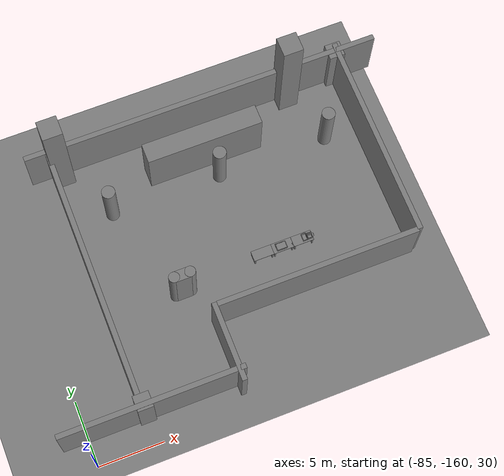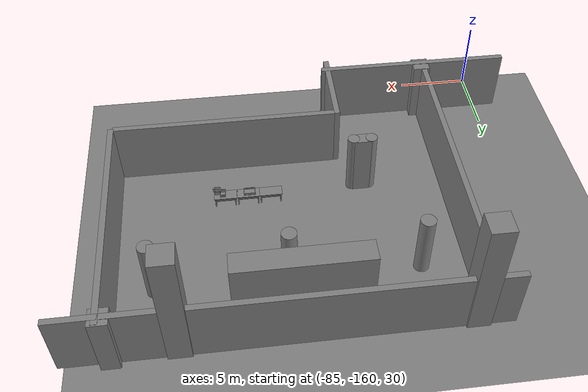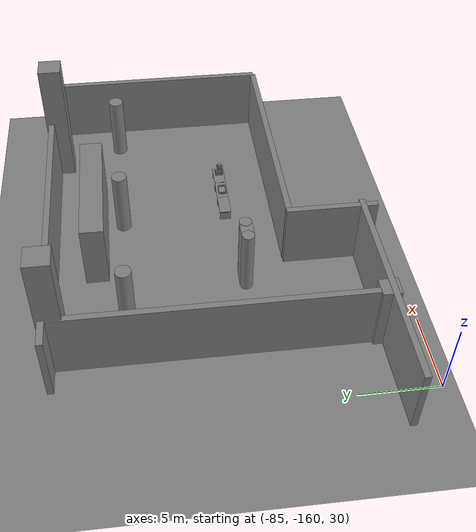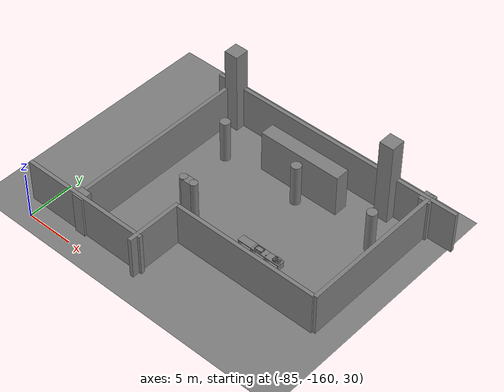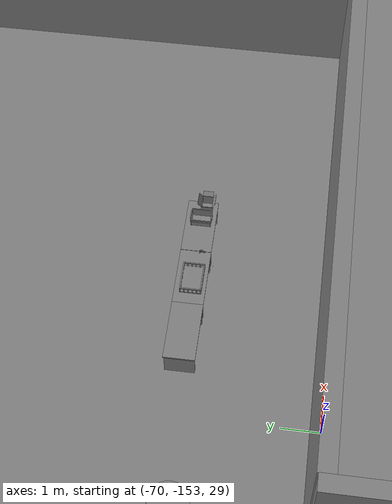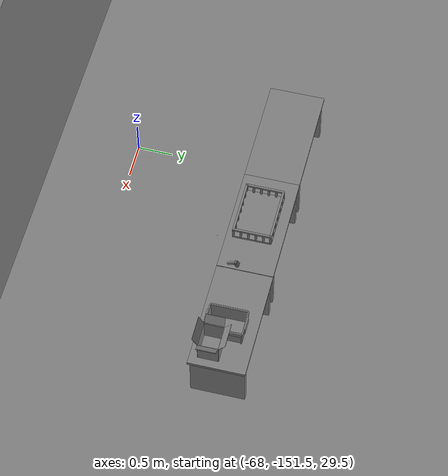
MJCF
<mujoco>
    <option gravity="0.000000000 0.000000000 -9.810000420" timestep="0.0049999999" integrator="implicitfast" density="1.225" viscosity="1.8000001e-05" noslip_iterations="10" iterations="100" sdf_iterations="50">
        <flag multiccd="disable"/>
    </option>
    <size memory="1000M"/>
    <compiler coordinate="local"/>
    <worldbody>
        <light cutoff="30" pos="0 1 1" dir="0 -1 -2"/>
        <light cutoff="30" pos="0 -1 1" dir="0 1 -2"/>
        <body pos="-64.866622925 -149.383972168 30.183746338" euler="89.999992371 89.999946594 0.000000000" name="openloong_gripper_2f85_fix_base_usda_bluebox_01">
            <geom contype="1" conaffinity="1" density="1000" type="box" material="" rgba="0.500000000 0.500000000 0.500000000 1.000000000" solimp="0.899999976 0.949999988 0.001000000" friction="1.000000000 0.005000000 0.000100000" solref="0.020000000 1.000000000" margin="0" condim="3" group="0" pos="0.276596069 0.187225342 0.000061035" quat="0.707107008 0.000077501 0.707106471 0.000077456" size="0.100000001 0.057999998 0.010000000" name="openloong_gripper_2f85_fix_base_usda_geom_0D2A8042_0B94_46FF_A330_EB3DCFBF3F45"/>
            <geom contype="1" conaffinity="1" density="1000" type="box" material="" rgba="0.500000000 0.500000000 0.500000000 1.000000000" solimp="0.899999976 0.949999988 0.001000000" friction="1.000000000 0.005000000 0.000100000" solref="0.020000000 1.000000000" margin="0" condim="3" group="0" pos="0.000000000 0.002883911 0.000000000" quat="1.000000000 0.000000000 0.000000000 0.000000000" size="0.254000008 0.003000000 0.172000006" name="openloong_gripper_2f85_fix_base_usda_geom_19D506B5_3757_419D_A38E_C5DCDA39F039"/>
            <geom contype="1" conaffinity="1" density="1000" type="box" material="" rgba="0.500000000 0.500000000 0.500000000 1.000000000" solimp="0.899999976 0.949999988 0.001000000" friction="1.000000000 0.005000000 0.000100000" solref="0.020000000 1.000000000" margin="0" condim="3" group="0" pos="0.000015259 0.124874115 0.173477173" quat="0.999796450 0.020176515 -0.000000015 0.000000030" size="0.259999990 0.119999997 0.007000000" name="openloong_gripper_2f85_fix_base_usda_geom_E642CCA8_B099_46DD_95EA_FC8B42222806"/>
            <geom contype="1" conaffinity="1" density="1000" type="box" material="" rgba="0.500000000 0.500000000 0.500000000 1.000000000" solimp="0.899999976 0.949999988 0.001000000" friction="1.000000000 0.005000000 0.000100000" solref="0.020000000 1.000000000" margin="0" condim="3" group="0" pos="0.000015259 0.124874115 -0.173477173" quat="0.999796450 -0.020176545 -0.000000015 0.000000000" size="0.259999990 0.119999997 0.007000000" name="openloong_gripper_2f85_fix_base_usda_geom_9449F99D_8619_483C_8952_B30FB21B86AA"/>
            <geom contype="1" conaffinity="1" density="1000" type="box" material="" rgba="0.500000000 0.500000000 0.500000000 1.000000000" solimp="0.899999976 0.949999988 0.001000000" friction="1.000000000 0.005000000 0.000100000" solref="0.020000000 1.000000000" margin="0" condim="3" group="0" pos="0.000015259 0.214012146 0.188980103" quat="0.999913096 0.013176724 0.000000015 0.000000000" size="0.259999990 0.029999999 0.012500000" name="openloong_gripper_2f85_fix_base_usda_geom_1DE6C1E9_87E1_4114_9F1B_A112128B79A0"/>
            <geom contype="1" conaffinity="1" density="1000" type="box" material="" rgba="0.500000000 0.500000000 0.500000000 1.000000000" solimp="0.899999976 0.949999988 0.001000000" friction="1.000000000 0.005000000 0.000100000" solref="0.020000000 1.000000000" margin="0" condim="3" group="0" pos="-0.258346558 0.125289917 0.001876831" quat="0.702796996 -0.020792052 0.710783184 0.020769238" size="0.189999998 0.119999997 0.009000000" name="openloong_gripper_2f85_fix_base_usda_geom_194EC42F_99CB_4DE3_847D_83AB405D72EB"/>
            <geom contype="1" conaffinity="1" density="1000" type="box" material="" rgba="0.500000000 0.500000000 0.500000000 1.000000000" solimp="0.899999976 0.949999988 0.001000000" friction="1.000000000 0.005000000 0.000100000" solref="0.020000000 1.000000000" margin="0" condim="3" group="0" pos="0.000015259 0.214012146 -0.188980103" quat="0.999913096 -0.013176769 0.000000030 0.000000015" size="0.259999990 0.029999999 0.012500000" name="openloong_gripper_2f85_fix_base_usda_geom_6A2B4B8B_E29E_4E47_87C1_C8632E17775F"/>
            <geom contype="1" conaffinity="1" density="1000" type="box" material="" rgba="0.500000000 0.500000000 0.500000000 1.000000000" solimp="0.899999976 0.949999988 0.001000000" friction="1.000000000 0.005000000 0.000100000" solref="0.020000000 1.000000000" margin="0" condim="3" group="0" pos="-0.276596069 0.187225342 0.000061035" quat="0.707106650 0.000077441 0.707106709 0.000077456" size="0.100000001 0.057999998 0.010000000" name="openloong_gripper_2f85_fix_base_usda_geom_DD2AB78F_50F2_4DE2_AE70_67680501DAEA"/>
            <geom contype="1" conaffinity="1" density="1000" type="box" material="" rgba="0.500000000 0.500000000 0.500000000 1.000000000" solimp="0.899999976 0.949999988 0.001000000" friction="1.000000000 0.005000000 0.000100000" solref="0.020000000 1.000000000" margin="0" condim="3" group="0" pos="0.258346558 0.125289917 0.001876831" quat="0.702851534 0.018856451 0.710823834 -0.019329429" size="0.189999998 0.119999997 0.009000000" name="openloong_gripper_2f85_fix_base_usda_geom_B8ACA76D_304B_4643_A5AC_C1393190D967"/>
            <freejoint name="openloong_gripper_2f85_fix_base_usda_bluebox_01_joint"/>
            <site size="0.005000000 0.005000000 0.005000000" rgba="0.500000000 0.500000000 0.500000000 1.000000000" pos="0.000000000 0.000000000 0.000000000" quat="0.999961913 0.008726534 0.000000000 0.000000000" group="0" type="sphere" name="openloong_gripper_2f85_fix_base_usda_bluebox_01site"/>
        </body>
        <body pos="-64.496299744 -149.491867065 30.235729218" euler="0.000000000 0.000000000 89.999946594" name="openloong_gripper_2f85_fix_base_usda_cardboardbox_01">
            <geom contype="1" conaffinity="1" density="1000" type="box" material="" rgba="0.500000000 0.500000000 0.500000000 1.000000000" solimp="0.899999976 0.949999988 0.001000000" friction="1.000000000 0.005000000 0.000100000" solref="0.020000000 1.000000000" margin="0" condim="3" group="0" pos="-0.003166199 -0.004086494 0.005052090" quat="1.000000000 0.000000000 0.000000000 0.000000000" size="0.142499998 0.177500010 0.005000000" name="openloong_gripper_2f85_fix_base_usda_geom_4CFB814D_991F_4BA9_B7CA_56E58BD3B8D1"/>
            <geom contype="1" conaffinity="1" density="1000" type="box" material="" rgba="0.500000000 0.500000000 0.500000000 1.000000000" solimp="0.899999976 0.949999988 0.001000000" friction="1.000000000 0.005000000 0.000100000" solref="0.020000000 1.000000000" margin="0" condim="3" group="0" pos="-0.003166199 0.170316696 0.150570869" quat="1.000000000 0.000000000 0.000000000 0.000000000" size="0.142499998 0.005000000 0.149999991" name="openloong_gripper_2f85_fix_base_usda_geom_919832EC_AA55_4429_9C97_DAE723CF52C4"/>
            <geom contype="1" conaffinity="1" density="1000" type="box" material="" rgba="0.500000000 0.500000000 0.500000000 1.000000000" solimp="0.899999976 0.949999988 0.001000000" friction="1.000000000 0.005000000 0.000100000" solref="0.020000000 1.000000000" margin="0" condim="3" group="0" pos="-0.147399902 -0.005307198 0.150570869" quat="1.000000000 0.000000000 0.000000000 0.000000000" size="0.005000000 0.177500010 0.149999991" name="openloong_gripper_2f85_fix_base_usda_geom_4E9F2BB3_F945_4428_A27F_BCFCEEF1D133"/>
            <geom contype="1" conaffinity="1" density="1000" type="box" material="" rgba="0.500000000 0.500000000 0.500000000 1.000000000" solimp="0.899999976 0.949999988 0.001000000" friction="1.000000000 0.005000000 0.000100000" solref="0.020000000 1.000000000" margin="0" condim="3" group="0" pos="0.140275955 -0.005307198 0.150570869" quat="1.000000000 0.000000000 0.000000000 0.000000000" size="0.005000000 0.177500010 0.149999991" name="openloong_gripper_2f85_fix_base_usda_geom_2732B486_4649_4BCB_84BA_AE30974C97CD"/>
            <geom contype="1" conaffinity="1" density="1000" type="box" material="" rgba="0.500000000 0.500000000 0.500000000 1.000000000" solimp="0.899999976 0.949999988 0.001000000" friction="1.000000000 0.005000000 0.000100000" solref="0.020000000 1.000000000" margin="0" condim="3" group="0" pos="-0.003166199 -0.181550980 0.150570869" quat="1.000000000 0.000000000 0.000000000 0.000000000" size="0.142499998 0.005000000 0.149999991" name="openloong_gripper_2f85_fix_base_usda_geom_EE8620DD_AC66_447A_82C1_1DE5F2D37C54"/>
            <freejoint name="openloong_gripper_2f85_fix_base_usda_cardboardbox_01_joint"/>
            <site size="0.005000000 0.005000000 0.005000000" rgba="0.500000000 0.500000000 0.500000000 1.000000000" pos="0.000000000 0.000000000 0.000000000" quat="0.999961913 0.008726535 0.000000000 0.000000000" group="0" type="sphere" name="openloong_gripper_2f85_fix_base_usda_site_B9B4B1B2_087A_41C5_A379_5431C7BB8DEC"/>
            <body pos="0.139160156 -0.004048347 0.301930904" euler="-179.999954224 49.383502960 179.999954224" name="openloong_gripper_2f85_fix_base_usda_A1_006">
                <geom contype="1" conaffinity="1" density="1000" type="box" material="" rgba="0.500000000 0.500000000 0.500000000 1.000000000" solimp="0.899999976 0.949999988 0.001000000" friction="1.000000000 0.005000000 0.000100000" solref="0.020000000 1.000000000" margin="0" condim="3" group="0" pos="-0.071587563 0.000009537 0.001745224" quat="0.999999881 0.000000000 0.000000000 0.000000000" size="0.071249999 0.179999992 0.002500000" name="openloong_gripper_2f85_fix_base_usda_geom_60772634_4E49_4E6B_8D8B_1DFFB4C3D2CD"/>
                <joint armature="0" stiffness="0.07" damping="0.0099999998" axis="0.000000 1.000000 0.000000" type="hinge" name="openloong_gripper_2f85_fix_base_usda_A1_006"/>
            </body>
            <body pos="-0.145902634 -0.004086494 0.301938057" euler="-180.000000000 -60.000011444 -180.000000000" name="openloong_gripper_2f85_fix_base_usda_A2_006">
                <geom contype="1" conaffinity="1" density="1000" type="box" material="" rgba="0.500000000 0.500000000 0.500000000 1.000000000" solimp="0.899999976 0.949999988 0.001000000" friction="1.000000000 0.005000000 0.000100000" solref="0.020000000 1.000000000" margin="0" condim="3" group="0" pos="0.071268082 0.000009537 0.002717972" quat="0.000002921 0.000000000 -0.000000030 0.999999881" size="0.071249999 0.179999992 0.002500000" name="openloong_gripper_2f85_fix_base_usda_geom_1ED85C47_C485_4BA7_BCC1_1666CBE92131"/>
                <joint armature="0" stiffness="0.07" damping="0.0099999998" axis="0.000000 1.000000 0.000000" type="hinge" name="openloong_gripper_2f85_fix_base_usda_A2_006"/>
            </body>
            <body pos="-0.003385544 0.175991058 0.301930904" euler="-125.858116150 -0.000004561 0.000002331" name="openloong_gripper_2f85_fix_base_usda_B2_006">
                <geom contype="1" conaffinity="1" density="1000" type="box" material="" rgba="0.500000000 0.500000000 0.500000000 1.000000000" solimp="0.899999976 0.949999988 0.001000000" friction="1.000000000 0.005000000 0.000100000" solref="0.020000000 1.000000000" margin="0" condim="3" group="0" pos="0.000009537 -0.070939064 -0.002470016" quat="0.999614120 0.027776197 -0.000000015 0.000000030" size="0.137500003 0.064999998 0.005000000" name="openloong_gripper_2f85_fix_base_usda_geom_96AB68D8_DBC5_4272_96EB_0E48D75BF977"/>
                <joint armature="0" stiffness="0.07" damping="0.0099999998" axis="1.000000 0.000000 0.000000" type="hinge" name="openloong_gripper_2f85_fix_base_usda_B2_006"/>
            </body>
            <body pos="-0.003385544 -0.184140205 0.301938057" euler="147.805557251 0.000000000 0.000000000" name="openloong_gripper_2f85_fix_base_usda_B1_006">
                <geom contype="1" conaffinity="1" density="1000" type="box" material="" rgba="0.500000000 0.500000000 0.500000000 1.000000000" solimp="0.899999976 0.949999988 0.001000000" friction="1.000000000 0.005000000 0.000100000" solref="0.020000000 1.000000000" margin="0" condim="3" group="0" pos="-0.000028610 0.070202351 -0.002703667" quat="0.999614179 -0.027776167 0.000000000 0.000000000" size="0.137500003 0.064999998 0.005000000" name="openloong_gripper_2f85_fix_base_usda_geom_B6F6DB56_0C79_4DAC_95CB_35E31E8F87E2"/>
                <joint armature="0" stiffness="0.07" damping="0.0099999998" axis="1.000000 0.000000 0.000000" type="hinge" name="openloong_gripper_2f85_fix_base_usda_B1_006"/>
            </body>
        </body>
        <body pos="-65.882858276 -149.481979370 30.229999542" euler="-64.487716675 0.000000000 0.000000000" name="openloong_gripper_2f85_fix_base_usda_Barcode">
            <geom contype="1" conaffinity="1" density="1000" type="box" material="" rgba="0.500000000 0.500000000 0.500000000 1.000000000" solimp="0.899999976 0.949999988 0.001000000" friction="1.000000000 0.005000000 0.000100000" solref="0.020000000 1.000000000" margin="0" condim="3" group="0" pos="0.000000000 0.013038635 0.001419067" quat="0.000000000 0.000000000 0.000000000 1.000000119" size="0.034000002 0.010000000 0.017999999" name="openloong_gripper_2f85_fix_base_usda_geom_760AA975_38BF_4EC3_A81B_6799F7FB5269"/>
            <geom contype="1" conaffinity="1" density="1000" type="box" material="" rgba="0.500000000 0.500000000 0.500000000 1.000000000" solimp="0.899999976 0.949999988 0.001000000" friction="1.000000000 0.005000000 0.000100000" solref="0.020000000 1.000000000" margin="0" condim="3" group="0" pos="0.000000000 -0.035301208 -0.007095337" quat="0.000000000 0.000000000 -0.043619365 0.999048233" size="0.028999999 0.010000000 0.020000000" name="openloong_gripper_2f85_fix_base_usda_geom_909C7FCC_3DCC_4EE8_88F2_0F4335C44999"/>
            <geom contype="1" conaffinity="1" density="1000" type="box" material="" rgba="0.500000000 0.500000000 0.500000000 1.000000000" solimp="0.899999976 0.949999988 0.001000000" friction="1.000000000 0.005000000 0.000100000" solref="0.020000000 1.000000000" margin="0" condim="3" group="0" pos="0.000000000 -0.043411255 -0.011749268" quat="0.922262907 0.386563420 0.000000000 0.000000000" size="0.026000001 0.010000000 0.020000000" name="openloong_gripper_2f85_fix_base_usda_geom_F066B2D5_EE2D_4278_9B28_448F5DF41805"/>
            <geom contype="1" conaffinity="1" density="1000" type="box" material="" rgba="0.500000000 0.500000000 0.500000000 1.000000000" solimp="0.899999976 0.949999988 0.001000000" friction="1.000000000 0.005000000 0.000100000" solref="0.020000000 1.000000000" margin="0" condim="3" group="0" pos="0.000000000 -0.016967773 -0.031860352" quat="0.000000000 0.000000000 0.000000000 1.000000119" size="0.008000000 0.010000000 0.013000000" name="openloong_gripper_2f85_fix_base_usda_geom_9D2C9837_2975_419A_A059_62F18B8B77B2"/>
            <geom contype="1" conaffinity="1" density="1000" type="box" material="" rgba="0.500000000 0.500000000 0.500000000 1.000000000" solimp="0.899999976 0.949999988 0.001000000" friction="1.000000000 0.005000000 0.000100000" solref="0.020000000 1.000000000" margin="0" condim="3" group="0" pos="0.000000000 -0.001869202 0.000312805" quat="0.953716993 0.300705761 0.000000000 0.000000000" size="0.032000002 0.010000000 0.018999999" name="openloong_gripper_2f85_fix_base_usda_geom_EEA01FE6_AC69_43FF_B83C_A5375C3AB3AB"/>
            <geom contype="1" conaffinity="1" density="1000" type="box" material="" rgba="0.500000000 0.500000000 0.500000000 1.000000000" solimp="0.899999976 0.949999988 0.001000000" friction="1.000000000 0.005000000 0.000100000" solref="0.020000000 1.000000000" margin="0" condim="3" group="0" pos="0.000000000 -0.019531250 -0.003173828" quat="0.953716993 0.300705761 0.000000000 0.000000000" size="0.030999999 0.010000000 0.020000000" name="openloong_gripper_2f85_fix_base_usda_geom_2622AC5B_CED0_41ED_B43E_BD2AE78F380C"/>
            <geom contype="1" conaffinity="1" density="1000" type="box" material="" rgba="0.500000000 0.500000000 0.500000000 1.000000000" solimp="0.899999976 0.949999988 0.001000000" friction="1.000000000 0.005000000 0.000100000" solref="0.020000000 1.000000000" margin="0" condim="3" group="0" pos="0.000000000 -0.035301208 -0.007095337" quat="0.953716993 0.300705761 0.000000000 0.000000000" size="0.028999999 0.010000000 0.020000000" name="openloong_gripper_2f85_fix_base_usda_geom_5D7118DC_3194_42D7_AA42_E885AF263E73"/>
            <geom contype="1" conaffinity="1" density="1000" type="box" material="" rgba="0.500000000 0.500000000 0.500000000 1.000000000" solimp="0.899999976 0.949999988 0.001000000" friction="1.000000000 0.005000000 0.000100000" solref="0.020000000 1.000000000" margin="0" condim="3" group="0" pos="0.000000000 -0.042617798 -0.071121216" quat="0.000000000 0.000000000 0.000000000 1.000000119" size="0.013000000 0.021000000 0.059999999" name="openloong_gripper_2f85_fix_base_usda_geom_65785FC2_52F6_4E0A_BAAA_F81960361082"/>
            <freejoint name="openloong_gripper_2f85_fix_base_usda_Barcode_joint"/>
            <site size="0.005000000 0.005000000 0.005000000" rgba="0.500000000 0.500000000 0.500000000 1.000000000" pos="0.000000000 0.000000000 0.000000000" quat="1.000000000 0.000000000 0.000000000 0.000000000" group="0" type="sphere" name="openloong_gripper_2f85_fix_base_usda_Barcode_site"/>
        </body>
        <body pos="-66.745018005 -149.392349243 30.184000015" euler="0.000000000 0.000000000 89.999946594" name="[22330665943445]_Basket_01">
            <geom contype="1" conaffinity="1" density="1000" type="box" material="" rgba="0.500000000 0.500000000 0.500000000 1.000000000" solimp="0.899999976 0.949999988 0.001000000" friction="1.000000000 0.005000000 0.000100000" solref="0.020000000 1.000000000" margin="0" condim="3" group="0" pos="-0.052425385 0.389207840 0.089787483" quat="0.707107008 0.000000000 0.000000000 0.707106411" size="0.014249999 0.014249999 0.059999999" name="[22330665943445]_geom_B77731AD_DBF8_40C5_98EE_A1A03EE880C9"/>
            <geom contype="1" conaffinity="1" density="1000" type="box" material="" rgba="0.500000000 0.500000000 0.500000000 1.000000000" solimp="0.899999976 0.949999988 0.001000000" friction="1.000000000 0.005000000 0.000100000" solref="0.020000000 1.000000000" margin="0" condim="3" group="0" pos="0.264015198 -0.133043289 0.089787483" quat="0.707107008 0.000000000 0.000000000 0.707106411" size="0.014249999 0.014249999 0.059999999" name="[22330665943445]_geom_537988A5_024D_4E79_B508_457E6166F0DB"/>
            <geom contype="1" conaffinity="1" density="1000" type="box" material="" rgba="0.500000000 0.500000000 0.500000000 1.000000000" solimp="0.899999976 0.949999988 0.001000000" friction="1.000000000 0.005000000 0.000100000" solref="0.020000000 1.000000000" margin="0" condim="3" group="0" pos="-0.264015198 -0.265548706 0.089793205" quat="0.707107008 0.000000000 0.000000000 0.707106411" size="0.014249999 0.014249999 0.059999999" name="[22330665943445]_geom_845585F9_605E_4A09_85CE_CE241DBE8C72"/>
            <geom contype="1" conaffinity="1" density="1000" type="box" material="" rgba="0.500000000 0.500000000 0.500000000 1.000000000" solimp="0.899999976 0.949999988 0.001000000" friction="1.000000000 0.005000000 0.000100000" solref="0.020000000 1.000000000" margin="0" condim="3" group="0" pos="-0.160263062 -0.389322281 0.089793205" quat="0.707107008 0.000000000 0.000000000 0.707106411" size="0.014249999 0.014249999 0.059999999" name="[22330665943445]_geom_0F047CB5_D1B5_4C23_AF21_DC5E63C274ED"/>
            <geom contype="1" conaffinity="1" density="1000" type="box" material="" rgba="0.500000000 0.500000000 0.500000000 1.000000000" solimp="0.899999976 0.949999988 0.001000000" friction="1.000000000 0.005000000 0.000100000" solref="0.020000000 1.000000000" margin="0" condim="3" group="0" pos="0.162265778 -0.389322281 0.089787483" quat="0.707107008 0.000000000 0.000000000 0.707106411" size="0.014249999 0.014249999 0.059999999" name="[22330665943445]_geom_496C8630_C2B2_47E5_8039_CE7E0DA71147"/>
            <geom contype="1" conaffinity="1" density="1000" type="box" material="" rgba="0.500000000 0.500000000 0.500000000 1.000000000" solimp="0.899999976 0.949999988 0.001000000" friction="1.000000000 0.005000000 0.000100000" solref="0.020000000 1.000000000" margin="0" condim="3" group="0" pos="0.264015198 0.389207840 0.089787483" quat="0.707107008 0.000000000 0.000000000 0.707106411" size="0.014249999 0.014249999 0.059999999" name="[22330665943445]_geom_D74A188B_6809_47D8_BA11_D9CF2F864E0B"/>
            <geom contype="1" conaffinity="1" density="1000" type="box" material="" rgba="0.500000000 0.500000000 0.500000000 1.000000000" solimp="0.899999976 0.949999988 0.001000000" friction="1.000000000 0.005000000 0.000100000" solref="0.020000000 1.000000000" margin="0" condim="3" group="0" pos="-0.264015198 -0.133043289 0.089793205" quat="0.707107008 0.000000000 0.000000000 0.707106411" size="0.014249999 0.014249999 0.059999999" name="[22330665943445]_geom_DEC9DEA5_9663_4663_B603_883801747B3F"/>
            <geom contype="1" conaffinity="1" density="1000" type="box" material="" rgba="0.500000000 0.500000000 0.500000000 1.000000000" solimp="0.899999976 0.949999988 0.001000000" friction="1.000000000 0.005000000 0.000100000" solref="0.020000000 1.000000000" margin="0" condim="3" group="0" pos="-0.264026642 0.269256592 0.089793205" quat="0.707107008 0.000000000 0.000000000 0.707106411" size="0.014249999 0.014249999 0.059999999" name="[22330665943445]_geom_E3AEA080_268A_46A5_82EE_E4DD42AB27FD"/>
            <geom contype="1" conaffinity="1" density="1000" type="box" material="" rgba="0.500000000 0.500000000 0.500000000 1.000000000" solimp="0.899999976 0.949999988 0.001000000" friction="1.000000000 0.005000000 0.000100000" solref="0.020000000 1.000000000" margin="0" condim="3" group="0" pos="0.054462433 0.389207840 0.089787483" quat="0.707107008 0.000000000 0.000000000 0.707106411" size="0.014249999 0.014249999 0.059999999" name="[22330665943445]_geom_8146CF3E_79AA_48EB_8F4F_BC1A4A509F3B"/>
            <geom contype="1" conaffinity="1" density="1000" type="box" material="" rgba="0.500000000 0.500000000 0.500000000 1.000000000" solimp="0.899999976 0.949999988 0.001000000" friction="1.000000000 0.005000000 0.000100000" solref="0.020000000 1.000000000" margin="0" condim="3" group="0" pos="0.054462433 -0.389322281 0.089787483" quat="0.707107008 0.000000000 0.000000000 0.707106411" size="0.014249999 0.014249999 0.059999999" name="[22330665943445]_geom_F889103B_C61B_423C_9AF8_9CD2B188E66A"/>
            <geom contype="1" conaffinity="1" density="1000" type="box" material="" rgba="0.500000000 0.500000000 0.500000000 1.000000000" solimp="0.899999976 0.949999988 0.001000000" friction="1.000000000 0.005000000 0.000100000" solref="0.020000000 1.000000000" margin="0" condim="3" group="0" pos="0.264015198 0.269256592 0.089793205" quat="0.707107008 0.000000000 0.000000000 0.707106411" size="0.014249999 0.014249999 0.059999999" name="[22330665943445]_geom_628FDFF3_997E_4576_B848_628131C381C0"/>
            <geom contype="1" conaffinity="1" density="1000" type="box" material="" rgba="0.500000000 0.500000000 0.500000000 1.000000000" solimp="0.899999976 0.949999988 0.001000000" friction="1.000000000 0.005000000 0.000100000" solref="0.020000000 1.000000000" margin="0" condim="3" group="0" pos="0.264015198 -0.389322281 0.089787483" quat="0.707107008 0.000000000 0.000000000 0.707106411" size="0.014249999 0.014249999 0.059999999" name="[22330665943445]_geom_A1C2881E_4416_4D8D_853A_182259530A34"/>
            <geom contype="1" conaffinity="1" density="1000" type="box" material="" rgba="0.500000000 0.500000000 0.500000000 1.000000000" solimp="0.899999976 0.949999988 0.001000000" friction="1.000000000 0.005000000 0.000100000" solref="0.020000000 1.000000000" margin="0" condim="3" group="0" pos="0.000000000 0.000000000 0.015998840" quat="0.707107008 0.000000000 0.000000000 0.707106411" size="0.403499991 0.279000014 0.015750000" name="[22330665943445]_geom_41719E3A_6D14_4483_9A53_EF42B35F87B3"/>
            <geom contype="1" conaffinity="1" density="1000" type="box" material="" rgba="0.500000000 0.500000000 0.500000000 1.000000000" solimp="0.899999976 0.949999988 0.001000000" friction="1.000000000 0.005000000 0.000100000" solref="0.020000000 1.000000000" margin="0" condim="3" group="0" pos="0.000000000 -0.389476776 0.163619041" quat="0.707107008 0.000000000 0.000000000 0.707106411" size="0.015000000 0.277500004 0.015750000" name="[22330665943445]_geom_45E29D02_FAD2_4251_9671_3F2656A71ECD"/>
            <geom contype="1" conaffinity="1" density="1000" type="box" material="" rgba="0.500000000 0.500000000 0.500000000 1.000000000" solimp="0.899999976 0.949999988 0.001000000" friction="1.000000000 0.005000000 0.000100000" solref="0.020000000 1.000000000" margin="0" condim="3" group="0" pos="0.162265778 0.389207840 0.089787483" quat="0.707107008 0.000000000 0.000000000 0.707106411" size="0.014249999 0.014249999 0.059999999" name="[22330665943445]_geom_3F8F48E8_1882_42C7_862D_D74A8D5AA648"/>
            <geom contype="1" conaffinity="1" density="1000" type="box" material="" rgba="0.500000000 0.500000000 0.500000000 1.000000000" solimp="0.899999976 0.949999988 0.001000000" friction="1.000000000 0.005000000 0.000100000" solref="0.020000000 1.000000000" margin="0" condim="3" group="0" pos="0.000000000 0.389471054 0.163619041" quat="0.707107008 0.000000000 0.000000000 0.707106411" size="0.015000000 0.277500004 0.015750000" name="[22330665943445]_geom_A531E85C_921F_4DE7_8319_ABC344DA7005"/>
            <geom contype="1" conaffinity="1" density="1000" type="box" material="" rgba="0.500000000 0.500000000 0.500000000 1.000000000" solimp="0.899999976 0.949999988 0.001000000" friction="1.000000000 0.005000000 0.000100000" solref="0.020000000 1.000000000" margin="0" condim="3" group="0" pos="-0.263511658 0.000000000 0.163619041" quat="0.707107008 0.000000000 0.000000000 0.707106411" size="0.403499991 0.015000000 0.015750000" name="[22330665943445]_geom_312C3887_821C_4D21_98D1_D81F46A46995"/>
            <geom contype="1" conaffinity="1" density="1000" type="box" material="" rgba="0.500000000 0.500000000 0.500000000 1.000000000" solimp="0.899999976 0.949999988 0.001000000" friction="1.000000000 0.005000000 0.000100000" solref="0.020000000 1.000000000" margin="0" condim="3" group="0" pos="-0.264015198 0.141334534 0.089793205" quat="0.707107008 0.000000000 0.000000000 0.707106411" size="0.014249999 0.014249999 0.059999999" name="[22330665943445]_geom_8F79153B_EBCB_4DB4_8C10_75169D28FFF1"/>
            <geom contype="1" conaffinity="1" density="1000" type="box" material="" rgba="0.500000000 0.500000000 0.500000000 1.000000000" solimp="0.899999976 0.949999988 0.001000000" friction="1.000000000 0.005000000 0.000100000" solref="0.020000000 1.000000000" margin="0" condim="3" group="0" pos="0.264015198 -0.265548706 0.089787483" quat="0.707107008 0.000000000 0.000000000 0.707106411" size="0.014249999 0.014249999 0.059999999" name="[22330665943445]_geom_00E5345E_2B6B_4443_8263_1B8748F0E778"/>
            <geom contype="1" conaffinity="1" density="1000" type="box" material="" rgba="0.500000000 0.500000000 0.500000000 1.000000000" solimp="0.899999976 0.949999988 0.001000000" friction="1.000000000 0.005000000 0.000100000" solref="0.020000000 1.000000000" margin="0" condim="3" group="0" pos="-0.160263062 0.389207840 0.089787483" quat="0.707107008 0.000000000 0.000000000 0.707106411" size="0.014249999 0.014249999 0.059999999" name="[22330665943445]_geom_50C82907_D5D2_4B78_9241_AC4B7DD6022D"/>
            <geom contype="1" conaffinity="1" density="1000" type="box" material="" rgba="0.500000000 0.500000000 0.500000000 1.000000000" solimp="0.899999976 0.949999988 0.001000000" friction="1.000000000 0.005000000 0.000100000" solref="0.020000000 1.000000000" margin="0" condim="3" group="0" pos="-0.052425385 -0.389322281 0.089787483" quat="0.707107008 0.000000000 0.000000000 0.707106411" size="0.014249999 0.014249999 0.059999999" name="[22330665943445]_geom_28B9CB66_BFA6_46B5_A583_DB82CCB5D514"/>
            <geom contype="1" conaffinity="1" density="1000" type="box" material="" rgba="0.500000000 0.500000000 0.500000000 1.000000000" solimp="0.899999976 0.949999988 0.001000000" friction="1.000000000 0.005000000 0.000100000" solref="0.020000000 1.000000000" margin="0" condim="3" group="0" pos="-0.264026642 -0.389322281 0.089793205" quat="0.707107008 0.000000000 0.000000000 0.707106411" size="0.014249999 0.014249999 0.059999999" name="[22330665943445]_geom_2F13EAAE_19E9_4E59_838F_92BD098F38A2"/>
            <geom contype="1" conaffinity="1" density="1000" type="box" material="" rgba="0.500000000 0.500000000 0.500000000 1.000000000" solimp="0.899999976 0.949999988 0.001000000" friction="1.000000000 0.005000000 0.000100000" solref="0.020000000 1.000000000" margin="0" condim="3" group="0" pos="0.264015198 0.141334534 0.089787483" quat="0.707107008 0.000000000 0.000000000 0.707106411" size="0.014249999 0.014249999 0.059999999" name="[22330665943445]_geom_A1723977_5CAE_4A2A_8BD7_CD7845B60828"/>
            <geom contype="1" conaffinity="1" density="1000" type="box" material="" rgba="0.500000000 0.500000000 0.500000000 1.000000000" solimp="0.899999976 0.949999988 0.001000000" friction="1.000000000 0.005000000 0.000100000" solref="0.020000000 1.000000000" margin="0" condim="3" group="0" pos="-0.264015198 0.389207840 0.089793205" quat="0.707107008 0.000000000 0.000000000 0.707106411" size="0.014249999 0.014249999 0.059999999" name="[22330665943445]_geom_2C67A7D6_CBDB_4BB9_9FB1_3BD3B4D85571"/>
            <geom contype="1" conaffinity="1" density="1000" type="box" material="" rgba="0.500000000 0.500000000 0.500000000 1.000000000" solimp="0.899999976 0.949999988 0.001000000" friction="1.000000000 0.005000000 0.000100000" solref="0.020000000 1.000000000" margin="0" condim="3" group="0" pos="0.264015198 0.004480362 0.089787483" quat="0.707107008 0.000000000 0.000000000 0.707106411" size="0.014249999 0.014249999 0.059999999" name="[22330665943445]_geom_5671FE5B_AA51_4C89_BABE_7B3B43DB0A65"/>
            <geom contype="1" conaffinity="1" density="1000" type="box" material="" rgba="0.500000000 0.500000000 0.500000000 1.000000000" solimp="0.899999976 0.949999988 0.001000000" friction="1.000000000 0.005000000 0.000100000" solref="0.020000000 1.000000000" margin="0" condim="3" group="0" pos="0.263694763 -0.000011444 0.163619041" quat="0.707107008 0.000000000 0.000000000 0.707106411" size="0.403499991 0.015000000 0.015750000" name="[22330665943445]_geom_A055EF35_D2DA_4562_9A2C_0BBEB8FBC4E3"/>
            <geom contype="1" conaffinity="1" density="1000" type="box" material="" rgba="0.500000000 0.500000000 0.500000000 1.000000000" solimp="0.899999976 0.949999988 0.001000000" friction="1.000000000 0.005000000 0.000100000" solref="0.020000000 1.000000000" margin="0" condim="3" group="0" pos="-0.264015198 0.004480362 0.089793205" quat="0.707107008 0.000000000 0.000000000 0.707106411" size="0.014249999 0.014249999 0.059999999" name="[22330665943445]_geom_9D6B6D58_5C01_4E37_9116_545CADC6D4AC"/>
            <freejoint name="[22330665943445]_joint_5050B6AE_6698_40F9_A8F3_D3B12D47B8CA"/>
        </body>
        <body pos="0.000000000 0.000000000 0.000000000" euler="0.000000000 0.000000000 0.000000000" name="Static Objects_Static Objects">
            <geom contype="1" conaffinity="1" density="1000" type="box" material="" rgba="0.500000000 0.500000000 0.500000000 1.000000000" solimp="0.899999976 0.949999988 0.001000000" friction="1.000000000 0.005000000 0.000100000" solref="0.020000000 1.000000000" margin="0" condim="3" group="0" pos="-67.544113159 -149.365814209 29.727830887" quat="0.500000417 0.499999970 0.499999553 0.499999970" size="0.381000012 0.319999993 0.041000001" name="Static Objects_geom_2AFE1F5C_3F79_480C_8F70_BEA610457A60"/>
            <geom contype="1" conaffinity="1" density="1000" type="box" material="" rgba="0.500000000 0.500000000 0.500000000 1.000000000" solimp="0.899999976 0.949999988 0.001000000" friction="1.000000000 0.005000000 0.000100000" solref="0.020000000 1.000000000" margin="0" condim="3" group="0" pos="-68.239501953 -149.365814209 30.086868286" quat="0.500000417 0.499999970 0.499999553 0.499999970" size="0.370999992 0.039500002 0.745000005" name="Static Objects_geom_D9FD9D2A_CC53_4D9B_8819_5DDDFBCAA688"/>
            <geom contype="1" conaffinity="1" density="1000" type="box" material="" rgba="0.500000000 0.500000000 0.500000000 1.000000000" solimp="0.899999976 0.949999988 0.001000000" friction="1.000000000 0.005000000 0.000100000" solref="0.020000000 1.000000000" margin="0" condim="3" group="0" pos="-68.239501953 -149.365814209 30.147235870" quat="0.500000417 0.499999970 0.499999553 0.499999970" size="0.400000006 0.022000000 0.800000012" name="Static Objects_geom_D875261E_4578_4819_B8D7_E0D899758C39"/>
            <geom contype="1" conaffinity="1" density="1000" type="box" material="" rgba="0.500000000 0.500000000 0.500000000 1.000000000" solimp="0.899999976 0.949999988 0.001000000" friction="1.000000000 0.005000000 0.000100000" solref="0.020000000 1.000000000" margin="0" condim="3" group="0" pos="-68.934890747 -149.365814209 29.727830887" quat="0.500000417 0.499999970 0.499999553 0.499999970" size="0.381000012 0.319999993 0.041000001" name="Static Objects_geom_157460BD_9C1A_46B1_A3CA_0836FA29F01D"/>
            <geom contype="1" conaffinity="1" density="1000" type="box" material="" rgba="0.500000000 0.500000000 0.500000000 1.000000000" solimp="0.899999976 0.949999988 0.001000000" friction="1.000000000 0.005000000 0.000100000" solref="0.020000000 1.000000000" margin="0" condim="3" group="0" pos="-68.239501953 -149.365814209 29.561563492" quat="0.500000417 0.499999970 0.499999553 0.499999970" size="0.020000000 0.022000000 0.660000026" name="Static Objects_geom_99B4B612_F0BA_47D1_9AA1_8F0CA292C1A1"/>
            <geom contype="1" conaffinity="1" density="1000" type="box" material="" rgba="0.500000000 0.500000000 0.500000000 1.000000000" solimp="0.899999976 0.949999988 0.001000000" friction="1.000000000 0.005000000 0.000100000" solref="0.020000000 1.000000000" margin="0" condim="3" group="0" pos="-65.945671082 -149.365814209 29.727830887" quat="0.500000417 0.499999970 0.499999553 0.499999970" size="0.381000012 0.319999993 0.041000001" name="Static Objects_geom_1F8299F6_2193_4C97_9222_ECF82865A7FF"/>
            <geom contype="1" conaffinity="1" density="1000" type="box" material="" rgba="0.500000000 0.500000000 0.500000000 1.000000000" solimp="0.899999976 0.949999988 0.001000000" friction="1.000000000 0.005000000 0.000100000" solref="0.020000000 1.000000000" margin="0" condim="3" group="0" pos="-66.641059875 -149.365814209 30.086868286" quat="0.500000417 0.499999970 0.499999553 0.499999970" size="0.370999992 0.039500002 0.745000005" name="Static Objects_geom_22ADB1F3_6454_4D50_9B2D_FABBD64ED75A"/>
            <geom contype="1" conaffinity="1" density="1000" type="box" material="" rgba="0.500000000 0.500000000 0.500000000 1.000000000" solimp="0.899999976 0.949999988 0.001000000" friction="1.000000000 0.005000000 0.000100000" solref="0.020000000 1.000000000" margin="0" condim="3" group="0" pos="-66.641059875 -149.365814209 30.147235870" quat="0.500000417 0.499999970 0.499999553 0.499999970" size="0.400000006 0.022000000 0.800000012" name="Static Objects_geom_F8FF03B5_BF19_4E0D_8150_AE1A3DFA9D59"/>
            <geom contype="1" conaffinity="1" density="1000" type="box" material="" rgba="0.500000000 0.500000000 0.500000000 1.000000000" solimp="0.899999976 0.949999988 0.001000000" friction="1.000000000 0.005000000 0.000100000" solref="0.020000000 1.000000000" margin="0" condim="3" group="0" pos="-67.336448669 -149.365814209 29.727830887" quat="0.500000417 0.499999970 0.499999553 0.499999970" size="0.381000012 0.319999993 0.041000001" name="Static Objects_geom_F338BD18_B778_44E5_8D0D_C0DD2FC6ADB4"/>
            <geom contype="1" conaffinity="1" density="1000" type="box" material="" rgba="0.500000000 0.500000000 0.500000000 1.000000000" solimp="0.899999976 0.949999988 0.001000000" friction="1.000000000 0.005000000 0.000100000" solref="0.020000000 1.000000000" margin="0" condim="3" group="0" pos="-66.641059875 -149.365814209 29.561563492" quat="0.500000417 0.499999970 0.499999553 0.499999970" size="0.020000000 0.022000000 0.660000026" name="Static Objects_geom_4EB7B8B3_F834_47FC_BDDD_0D5AEF202036"/>
            <geom contype="1" conaffinity="1" density="1000" type="box" material="" rgba="0.500000000 0.500000000 0.500000000 1.000000000" solimp="0.899999976 0.949999988 0.001000000" friction="1.000000000 0.005000000 0.000100000" solref="0.020000000 1.000000000" margin="0" condim="3" group="0" pos="-64.338577271 -149.365814209 29.727830887" quat="0.500000417 0.499999970 0.499999553 0.499999970" size="0.381000012 0.319999993 0.041000001" name="Static Objects_geom_EC904029_676D_4048_A2FE_DCFF28869A75"/>
            <geom contype="1" conaffinity="1" density="1000" type="box" material="" rgba="0.500000000 0.500000000 0.500000000 1.000000000" solimp="0.899999976 0.949999988 0.001000000" friction="1.000000000 0.005000000 0.000100000" solref="0.020000000 1.000000000" margin="0" condim="3" group="0" pos="-65.033966064 -149.365814209 30.086868286" quat="0.500000417 0.499999970 0.499999553 0.499999970" size="0.370999992 0.039500002 0.745000005" name="Static Objects_geom_75BD4209_875A_4AA6_9048_32E1B7794DE0"/>
            <geom contype="1" conaffinity="1" density="1000" type="box" material="" rgba="0.500000000 0.500000000 0.500000000 1.000000000" solimp="0.899999976 0.949999988 0.001000000" friction="1.000000000 0.005000000 0.000100000" solref="0.020000000 1.000000000" margin="0" condim="3" group="0" pos="-65.033966064 -149.365814209 30.147235870" quat="0.500000417 0.499999970 0.499999553 0.499999970" size="0.400000006 0.022000000 0.800000012" name="Static Objects_geom_ED36A484_53E9_4C16_99FD_8ABD2F8DE614"/>
            <geom contype="1" conaffinity="1" density="1000" type="box" material="" rgba="0.500000000 0.500000000 0.500000000 1.000000000" solimp="0.899999976 0.949999988 0.001000000" friction="1.000000000 0.005000000 0.000100000" solref="0.020000000 1.000000000" margin="0" condim="3" group="0" pos="-65.729354858 -149.365814209 29.727830887" quat="0.500000417 0.499999970 0.499999553 0.499999970" size="0.381000012 0.319999993 0.041000001" name="Static Objects_geom_9297FBCD_EC87_48F4_BFA0_1B782A815DE9"/>
            <geom contype="1" conaffinity="1" density="1000" type="box" material="" rgba="0.500000000 0.500000000 0.500000000 1.000000000" solimp="0.899999976 0.949999988 0.001000000" friction="1.000000000 0.005000000 0.000100000" solref="0.020000000 1.000000000" margin="0" condim="3" group="0" pos="-65.033966064 -149.365814209 29.561563492" quat="0.500000417 0.499999970 0.499999553 0.499999970" size="0.020000000 0.022000000 0.660000026" name="Static Objects_geom_173B5BFB_5AC8_43EF_8094_A991E9896AC7"/>
            <geom contype="1" conaffinity="1" density="1000" type="box" material="" rgba="0.500000000 0.500000000 0.500000000 1.000000000" solimp="0.899999976 0.949999988 0.001000000" friction="1.000000000 0.005000000 0.000100000" solref="0.020000000 1.000000000" margin="0" condim="3" group="0" pos="-61.754566193 -137.853729248 33.906845093" quat="0.707107067 0.000000000 0.000000000 0.707106471" size="0.759999990 0.759999990 4.500000000" name="Static Objects_geom_4DF9E104_D078_432C_B0A3_D57AD82E6990"/>
            <geom contype="1" conaffinity="1" density="1000" type="box" material="" rgba="0.500000000 0.500000000 0.500000000 1.000000000" solimp="0.899999976 0.949999988 0.001000000" friction="1.000000000 0.005000000 0.000100000" solref="0.020000000 1.000000000" margin="0" condim="3" group="0" pos="-57.511135101 -144.927108765 31.707921982" quat="1.000000000 0.000000000 0.000000000 0.000000000" size="0.200000003 8.000000000 2.299999952" name="Static Objects_geom_9CE0A327_11A9_4761_8A89_D05D773D1E6A"/>
            <geom contype="1" conaffinity="1" density="1000" type="box" material="" rgba="0.500000000 0.500000000 0.500000000 1.000000000" solimp="0.899999976 0.949999988 0.001000000" friction="1.000000000 0.005000000 0.000100000" solref="0.020000000 1.000000000" margin="0" condim="3" group="0" pos="-80.517646790 -157.574050903 31.688196182" quat="0.707107067 0.000000000 0.000000000 0.707106471" size="0.600000024 0.600000024 2.299999952" name="Static Objects_geom_00E07758_BDBF_4B59_A97E_661CE166E10F"/>
            <geom contype="1" conaffinity="1" density="1000" type="box" material="" rgba="0.500000000 0.500000000 0.500000000 1.000000000" solimp="0.899999976 0.949999988 0.001000000" friction="1.000000000 0.005000000 0.000100000" solref="0.020000000 1.000000000" margin="0" condim="3" group="0" pos="-80.711044312 -147.414932251 31.666158676" quat="1.000000000 0.000000000 0.000000000 0.000000000" size="0.200000003 10.000000000 2.299999952" name="Static Objects_geom_E4E9AE1C_F982_42DB_8658_6AE70B4A63F3"/>
            <geom contype="1" conaffinity="1" density="1000" type="box" material="" rgba="0.500000000 0.500000000 0.500000000 1.000000000" solimp="0.899999976 0.949999988 0.001000000" friction="1.000000000 0.005000000 0.000100000" solref="0.020000000 1.000000000" margin="0" condim="3" group="0" pos="-57.687217712 -137.434692383 31.688196182" quat="0.707107067 0.000000000 0.000000000 0.707106471" size="0.600000024 0.600000024 2.299999952" name="Static Objects_geom_A8B52718_FD6C_4365_AAF3_62576D9B18A1"/>
            <geom contype="1" conaffinity="1" density="1000" type="box" material="" rgba="0.500000000 0.500000000 0.500000000 1.000000000" solimp="0.899999976 0.949999988 0.001000000" friction="1.000000000 0.005000000 0.000100000" solref="0.020000000 1.000000000" margin="0" condim="3" group="0" pos="-69.537033081 -140.263229370 31.714921951" quat="0.707107067 0.000000000 0.000000000 0.707106471" size="0.759999990 4.500000000 2.299999952" name="Static Objects_geom_97D29004_9059_46E8_B696_B3AAA9AE3EE8"/>
            <geom contype="1" conaffinity="1" density="1000" type="box" material="" rgba="0.500000000 0.500000000 0.500000000 1.000000000" solimp="0.899999976 0.949999988 0.001000000" friction="1.000000000 0.005000000 0.000100000" solref="0.020000000 1.000000000" margin="0" condim="3" group="0" pos="-80.073638916 -137.853713989 33.906845093" quat="0.707107067 0.000000000 0.000000000 0.707106471" size="0.759999990 0.759999990 4.500000000" name="Static Objects_geom_54DFAA9E_612A_4974_A768_70C5BAC6BE51"/>
            <geom contype="1" conaffinity="1" density="1000" type="box" material="" rgba="0.500000000 0.500000000 0.500000000 1.000000000" solimp="0.899999976 0.949999988 0.001000000" friction="1.000000000 0.005000000 0.000100000" solref="0.020000000 1.000000000" margin="0" condim="3" group="0" pos="-73.406707764 -155.734664917 31.707921982" quat="1.000000000 0.000000000 0.000000000 0.000000000" size="0.200000003 3.000000000 2.299999952" name="Static Objects_geom_E45DAB46_A42C_401B_B118_F7166575A6BA"/>
            <geom contype="1" conaffinity="1" density="1000" type="box" material="" rgba="0.500000000 0.500000000 0.500000000 1.000000000" solimp="0.899999976 0.949999988 0.001000000" friction="1.000000000 0.005000000 0.000100000" solref="0.020000000 1.000000000" margin="0" condim="3" group="0" pos="-68.497543335 -137.448257446 31.707921982" quat="0.707107067 0.000000000 0.000000000 0.707106471" size="0.200000003 14.000000000 2.299999952" name="Static Objects_geom_C6A6E1EF_7675_4B07_9BFF_659AE7EA4F88"/>
            <geom contype="1" conaffinity="1" density="1000" type="cylinder" material="" rgba="0.500000000 0.500000000 0.500000000 1.000000000" solimp="0.899999976 0.949999988 0.001000000" friction="1.000000000 0.005000000 0.000100000" solref="0.020000000 1.000000000" margin="0" condim="3" group="0" pos="-68.868522644 -142.134506226 31.711090088" quat="0.707107067 0.000000000 0.000000000 0.707106471" size="0.509999990 2.299999952 1.000000000" name="Static Objects_geom_A20C5F11_525A_4C54_A7CC_360A6E2997AD"/>
            <geom contype="1" conaffinity="1" density="1000" type="plane" material="" rgba="0.500000000 0.500000000 0.500000000 1.000000000" solimp="0.899999976 0.949999988 0.001000000" friction="1.000000000 0.005000000 0.000100000" solref="0.020000000 1.000000000" margin="0" condim="3" group="0" pos="-72.873703003 -147.131927490 29.409669876" quat="1.000000000 0.000000000 0.000000000 0.000000000" size="18.000000000 14.000000000 1.000000000" name="Static Objects_geom_D7599554_E89B_4C4E_8BF2_4ABD9C010F93"/>
            <geom contype="1" conaffinity="1" density="1000" type="box" material="" rgba="0.500000000 0.500000000 0.500000000 1.000000000" solimp="0.899999976 0.949999988 0.001000000" friction="1.000000000 0.005000000 0.000100000" solref="0.020000000 1.000000000" margin="0" condim="3" group="0" pos="-79.943580627 -157.782272339 31.707921982" quat="0.707107067 0.000000000 0.000000000 0.707106471" size="0.200000003 7.000000000 2.299999952" name="Static Objects_geom_15133A06_1D51_44EB_AD62_1ABF839597EC"/>
            <geom contype="1" conaffinity="1" density="1000" type="box" material="" rgba="0.500000000 0.500000000 0.500000000 1.000000000" solimp="0.899999976 0.949999988 0.001000000" friction="1.000000000 0.005000000 0.000100000" solref="0.020000000 1.000000000" margin="0" condim="3" group="0" pos="-65.421028137 -152.903442383 31.707921982" quat="0.707107067 0.000000000 0.000000000 0.707106471" size="0.200000003 7.800000191 2.299999952" name="Static Objects_geom_EF99FA4C_C32E_406C_B194_679F5A639332"/>
            <geom contype="1" conaffinity="1" density="1000" type="box" material="" rgba="0.500000000 0.500000000 0.500000000 1.000000000" solimp="0.899999976 0.949999988 0.001000000" friction="1.000000000 0.005000000 0.000100000" solref="0.020000000 1.000000000" margin="0" condim="3" group="0" pos="-74.776908875 -149.964416504 31.688196182" quat="1.000000000 0.000000000 0.000000000 0.000000000" size="0.600000024 0.409999996 2.299999952" name="Static Objects_geom_F1B63CC8_FA89_4267_9069_AB4D334A3889"/>
            <geom contype="1" conaffinity="1" density="1000" type="cylinder" material="" rgba="0.500000000 0.500000000 0.500000000 1.000000000" solimp="0.899999976 0.949999988 0.001000000" friction="1.000000000 0.005000000 0.000100000" solref="0.020000000 1.000000000" margin="0" condim="3" group="0" pos="-60.161884308 -142.134506226 31.711090088" quat="0.707107067 0.000000000 0.000000000 0.707106471" size="0.509999990 2.299999952 1.000000000" name="Static Objects_geom_FAB3C282_1D7D_40F2_B478_DAFCB4C1BC0B"/>
            <geom contype="1" conaffinity="1" density="1000" type="cylinder" material="" rgba="0.500000000 0.500000000 0.500000000 1.000000000" solimp="0.899999976 0.949999988 0.001000000" friction="1.000000000 0.005000000 0.000100000" solref="0.020000000 1.000000000" margin="0" condim="3" group="0" pos="-75.382453918 -149.963455200 31.711090088" quat="0.707107067 0.000000000 0.000000000 0.707106471" size="0.409999996 2.299999952 1.000000000" name="Static Objects_geom_E03FA04C_4834_4417_ACA0_63EBA2FBB66D"/>
            <geom contype="1" conaffinity="1" density="1000" type="cylinder" material="" rgba="0.500000000 0.500000000 0.500000000 1.000000000" solimp="0.899999976 0.949999988 0.001000000" friction="1.000000000 0.005000000 0.000100000" solref="0.020000000 1.000000000" margin="0" condim="3" group="0" pos="-74.154960632 -149.963455200 31.711090088" quat="0.707107067 0.000000000 0.000000000 0.707106471" size="0.409999996 2.299999952 1.000000000" name="Static Objects_geom_7B3B1CC8_28AF_456C_8E95_1C96773961C6"/>
            <geom contype="1" conaffinity="1" density="1000" type="cylinder" material="" rgba="0.500000000 0.500000000 0.500000000 1.000000000" solimp="0.899999976 0.949999988 0.001000000" friction="1.000000000 0.005000000 0.000100000" solref="0.020000000 1.000000000" margin="0" condim="3" group="0" pos="-77.566612244 -142.134506226 31.711090088" quat="0.707107067 0.000000000 0.000000000 0.707106471" size="0.509999990 2.299999952 1.000000000" name="Static Objects_geom_64D884FE_B625_4250_A005_9B527C3067F9"/>
        </body>
        <body pos="-66.291030884 -149.869689941 29.018842697" euler="0.000000000 0.000000000 89.999946594" mocap="true" name="openloong_gripper_2f85_fix_base_usda_leftHandMocap"/>
        <body pos="-66.291030884 -149.869689941 29.018842697" euler="0.000000000 0.000000000 89.999946594" mocap="true" name="openloong_gripper_2f85_fix_base_usda_rightHandMocap"/>
        <body pos="-66.291030884 -149.869689941 30.218843460" euler="0.000000000 0.000000000 89.999946594" name="openloong_gripper_2f85_fix_base_usda_base_link">
            <geom contype="1" conaffinity="1" density="1000" type="mesh" material="" rgba="0.783999979 0.783999979 0.783999979 1.000000000" solimp="0.899999976 0.949999988 0.001000000" friction="1.000000000 0.005000000 0.000100000" solref="0.020000000 1.000000000" margin="0" condim="3" group="3" mesh="base_link" pos="0.000000000 0.000000000 0.000000000" quat="1.000000000 0.000000000 0.000000000 0.000000000" size="1.000000000 1.000000000 1.000000000" name="openloong_gripper_2f85_fix_base_usda__geom_7_E11C070C_D350_4041_9B87_C8AF74F660D5"/>
            <site size="0.005000000 0.005000000 0.005000000" rgba="0.500000000 0.500000000 0.500000000 1.000000000" pos="0.000000000 0.000000000 0.000000000" quat="1.000000000 0.000000000 0.000000000 0.000000000" group="0" type="sphere" name="openloong_gripper_2f85_fix_base_usda_imu"/>
            <inertial mass="22.447001" pos="-0.005664100 -0.001336700 0.238289997" diaginertia="0.374352545 0.277180195 0.220617250" quat="0.999247074 0.035235517 -0.015086859 0.006023135"/>
            <body pos="0.000000000 0.000000000 0.299997330" euler="0.000000000 0.000000000 0.000000000" name="openloong_gripper_2f85_fix_base_usda_dummy_body">
                <geom contype="1" conaffinity="1" density="1000" type="sphere" material="" rgba="0.783999979 0.783999979 0.783999979 1.000000000" solimp="0.899999976 0.949999988 0.001000000" friction="1.000000000 0.005000000 0.000100000" solref="0.020000000 1.000000000" margin="0" condim="3" group="3" pos="0.000000000 0.000000000 0.000000000" quat="1.000000000 0.000000000 0.000000000 0.000000000" size="0.010000000 0.000000000 0.000000000" name="openloong_gripper_2f85_fix_base_usda__geom_8_102A6BEA_3CD0_4561_A1BD_50029BB4B7D1"/>
                <joint armature="0.0099999998" stiffness="0" damping="0.1" axis="0.000000 0.000000 1.000000" type="hinge" name="openloong_gripper_2f85_fix_base_usda_dummy_joint"/>
                <site size="0.010000000 0.005000000 0.005000000" rgba="0.500000000 0.500000000 0.500000000 1.000000000" pos="0.000000000 0.000000000 0.000000000" quat="1.000000000 0.000000000 0.000000000 0.000000000" group="3" type="sphere" name="openloong_gripper_2f85_fix_base_usda_dummy_site"/>
            </body>
            <body pos="0.009002686 0.000000000 0.406400681" euler="0.000000000 0.000000000 0.000000000" name="openloong_gripper_2f85_fix_base_usda_Link_head_yaw">
                <geom contype="1" conaffinity="1" density="1000" type="mesh" material="" rgba="0.783999979 0.783999979 0.783999979 1.000000000" solimp="0.899999976 0.949999988 0.001000000" friction="1.000000000 0.005000000 0.000100000" solref="0.020000000 1.000000000" margin="0" condim="3" group="3" mesh="Link_head_yaw" pos="0.000000000 0.000000000 0.000000000" quat="1.000000000 0.000000000 0.000000000 0.000000000" size="1.000000000 1.000000000 1.000000000" name="openloong_gripper_2f85_fix_base_usda__geom_10_ADDDF446_804B_45BC_9C8B_93C43F9890FC"/>
                <inertial mass="0.84249002" pos="0.000000000 -0.002081400 0.044801001" diaginertia="0.000700588 0.000629000 0.000553812" quat="0.706933022 -0.015675601 0.015677100 0.706933022"/>
                <body pos="0.000000000 -0.034599304 0.048500061" euler="0.000000000 0.000000000 0.000000000" name="openloong_gripper_2f85_fix_base_usda_Link_head_pitch">
                    <geom contype="1" conaffinity="1" density="1000" type="mesh" material="" rgba="0.783999979 0.783999979 0.783999979 1.000000000" solimp="0.899999976 0.949999988 0.001000000" friction="1.000000000 0.005000000 0.000100000" solref="0.020000000 1.000000000" margin="0" condim="3" group="3" mesh="Link_head_pitch" pos="0.000000000 0.000000000 0.000000000" quat="1.000000000 0.000000000 0.000000000 0.000000000" size="1.000000000 1.000000000 1.000000000" name="openloong_gripper_2f85_fix_base_usda__geom_12_3D0BBE16_7A9B_46A9_940B_3ABF04580FCD"/>
                    <inertial mass="1.3943" pos="0.020569000 0.033004001 0.125000000" diaginertia="0.006381400 0.006289940 0.004481460" quat="0.973390222 0.008406822 0.228157058 0.019624906"/>
                    <body pos="0.000000000 0.029998779 0.000000000" euler="0.000000000 0.000000000 0.000000000" name="openloong_gripper_2f85_fix_base_usda_neck_center_body">
                        <site size="0.010000000 0.005000000 0.005000000" rgba="0.500000000 0.500000000 0.500000000 1.000000000" pos="0.000000000 0.000000000 0.000000000" quat="1.000000000 0.000000000 0.000000000 0.000000000" group="3" type="sphere" name="openloong_gripper_2f85_fix_base_usda_neck_center_site"/>
                        <body pos="0.020004272 0.000000000 0.149999619" euler="-0.000002229 39.998176575 -90.000205994" name="openloong_gripper_2f85_fix_base_usda_camera_head">
                            <site size="0.010000000 0.005000000 0.005000000" rgba="0.500000000 0.500000000 0.500000000 1.000000000" pos="0.000000000 0.000000000 0.000000000" quat="1.000000000 0.000000000 0.000000000 0.000000000" group="3" type="sphere" name="openloong_gripper_2f85_fix_base_usda_camera_head_site"/>
                        </body>
                    </body>
                </body>
            </body>
            <body pos="0.003997803 -0.161598206 0.392200470" euler="0.000000000 0.000000000 0.000000000" name="openloong_gripper_2f85_fix_base_usda_Link_arm_r_01">
                <geom contype="1" conaffinity="1" density="1000" type="mesh" material="" rgba="0.783999979 0.783999979 0.783999979 1.000000000" solimp="0.899999976 0.949999988 0.001000000" friction="1.000000000 0.005000000 0.000100000" solref="0.020000000 1.000000000" margin="0" condim="3" group="3" mesh="Link_arm_r_01" pos="0.000000000 0.000000000 0.000000000" quat="1.000000000 0.000000000 0.000000000 0.000000000" size="1.000000000 1.000000000 1.000000000" name="openloong_gripper_2f85_fix_base_usda__geom_14_503DB94A_831E_4917_AE41_2AE22CEF61FE"/>
                <joint armature="0.0099999998" stiffness="0" damping="1" axis="0.000000 -1.000000 0.000000" limited="true" range="-170.000015259 170.000015259" type="hinge" name="openloong_gripper_2f85_fix_base_usda_J_arm_r_01"/>
                <inertial mass="0.75641" pos="0.004494600 -0.038293999 -0.000001874" diaginertia="0.000842990 0.000803050 0.000587120" quat="-0.000163502 0.707098067 0.000812463 0.707115054"/>
                <body pos="-0.041992188 -0.041000366 0.000000000" euler="0.000000000 0.000000000 0.000000000" name="openloong_gripper_2f85_fix_base_usda_Link_arm_r_02">
                    <geom contype="1" conaffinity="1" density="1000" type="mesh" material="" rgba="0.783999979 0.783999979 0.783999979 1.000000000" solimp="0.899999976 0.949999988 0.001000000" friction="1.000000000 0.005000000 0.000100000" solref="0.020000000 1.000000000" margin="0" condim="3" group="3" mesh="Link_arm_r_02" pos="0.000000000 0.000000000 0.000000000" quat="1.000000000 0.000000000 0.000000000 0.000000000" size="1.000000000 1.000000000 1.000000000" name="openloong_gripper_2f85_fix_base_usda__geom_16_4E6351F7_504B_40E5_BE21_3E6300F27F4B"/>
                    <joint armature="0.0099999998" stiffness="0" damping="1" axis="-1.000000 0.000000 0.000000" limited="true" range="-105.000244141 105.000244141" type="hinge" name="openloong_gripper_2f85_fix_base_usda_J_arm_r_02"/>
                    <inertial mass="0.98500001" pos="0.041999999 -0.067430697 0.000000000" diaginertia="0.002262690 0.001730990 0.001154020" quat="0.500000000 0.500000000 -0.500000000 0.500000000"/>
                    <body pos="0.041992188 -0.122596741 0.000000000" euler="0.000000000 0.000000000 0.000000000" name="openloong_gripper_2f85_fix_base_usda_Link_arm_r_03">
                        <geom contype="1" conaffinity="1" density="1000" type="mesh" material="" rgba="0.783999979 0.783999979 0.783999979 1.000000000" solimp="0.899999976 0.949999988 0.001000000" friction="1.000000000 0.005000000 0.000100000" solref="0.020000000 1.000000000" margin="0" condim="3" group="3" mesh="Link_arm_r_03" pos="0.000000000 0.000000000 0.000000000" quat="1.000000000 0.000000000 0.000000000 0.000000000" size="1.000000000 1.000000000 1.000000000" name="openloong_gripper_2f85_fix_base_usda__geom_18_95309CD6_5E22_44DE_82BB_739FD2FED153"/>
                        <joint armature="0.0099999998" stiffness="0" damping="1" axis="0.000000 -1.000000 0.000000" limited="true" range="-170.000015259 170.000015259" type="hinge" name="openloong_gripper_2f85_fix_base_usda_J_arm_r_03"/>
                        <inertial mass="0.95899999" pos="-0.001413580 -0.164663002 0.020757901" diaginertia="0.002101340 0.002064590 0.000754802" quat="0.560480952 0.454391927 -0.443732947 0.531497955"/>
                        <body pos="0.035293579 -0.177406311 0.023998260" euler="0.000000000 0.000000000 0.000000000" name="openloong_gripper_2f85_fix_base_usda_Link_arm_r_04">
                            <geom contype="1" conaffinity="1" density="1000" type="mesh" material="" rgba="0.783999979 0.783999979 0.783999979 1.000000000" solimp="0.899999976 0.949999988 0.001000000" friction="1.000000000 0.005000000 0.000100000" solref="0.020000000 1.000000000" margin="0" condim="3" group="3" mesh="Link_arm_r_04" pos="0.000000000 0.000000000 0.000000000" quat="1.000000000 0.000000000 0.000000000 0.000000000" size="1.000000000 1.000000000 1.000000000" name="openloong_gripper_2f85_fix_base_usda__geom_20_5186F778_A9F6_439B_B85E_A7BC73632390"/>
                            <joint armature="0.0099999998" stiffness="0" damping="1" axis="-1.000000 0.000000 0.000000" limited="true" range="0.000000000 170.000015259" type="hinge" name="openloong_gripper_2f85_fix_base_usda_J_arm_r_04"/>
                            <inertial mass="0.60000002" pos="-0.038727000 -0.060766999 -0.021003000" diaginertia="0.001092610 0.000712422 0.000645102" quat="0.327701002 0.632602990 -0.467366993 0.523443997"/>
                            <body pos="-0.035293579 -0.103492737 -0.023998260" euler="0.000000000 0.000000000 0.000000000" name="openloong_gripper_2f85_fix_base_usda_Link_arm_r_05">
                                <geom contype="1" conaffinity="1" density="1000" type="mesh" material="" rgba="0.783999979 0.783999979 0.783999979 1.000000000" solimp="0.899999976 0.949999988 0.001000000" friction="1.000000000 0.005000000 0.000100000" solref="0.020000000 1.000000000" margin="0" condim="3" group="3" mesh="Link_arm_r_05" pos="0.000000000 0.000000000 0.000000000" quat="1.000000000 0.000000000 0.000000000 0.000000000" size="1.000000000 1.000000000 1.000000000" name="openloong_gripper_2f85_fix_base_usda__geom_22_392309C0_772B_42A3_BB16_1866767B1B50"/>
                                <joint armature="0.0099999998" stiffness="0" damping="1" axis="0.000000 -1.000000 0.000000" limited="true" range="-170.000015259 170.000015259" type="hinge" name="openloong_gripper_2f85_fix_base_usda_J_arm_r_05"/>
                                <inertial mass="0.68976003" pos="0.000032712 -0.068658002 -0.000111780" diaginertia="0.002522510 0.002411100 0.000448695" quat="0.707660973 0.706543028 -0.002603360 0.002470550"/>
                                <body pos="-0.026489258 -0.196502686 0.000000000" euler="0.000000000 0.000000000 0.000000000" name="openloong_gripper_2f85_fix_base_usda_Link_arm_r_06">
                                    <geom contype="1" conaffinity="1" density="1000" type="mesh" material="" rgba="0.783999979 0.783999979 0.783999979 1.000000000" solimp="0.899999976 0.949999988 0.001000000" friction="1.000000000 0.005000000 0.000100000" solref="0.020000000 1.000000000" margin="0" condim="3" group="3" mesh="Link_arm_r_06" pos="0.000000000 0.000000000 0.000000000" quat="1.000000000 0.000000000 0.000000000 0.000000000" size="1.000000000 1.000000000 1.000000000" name="openloong_gripper_2f85_fix_base_usda__geom_24_C4110337_8152_4101_810F_98A3B734FA49"/>
                                    <joint armature="0.0099999998" stiffness="0" damping="1" axis="1.000000 0.000000 0.000000" limited="true" range="-105.000244141 105.000244141" type="hinge" name="openloong_gripper_2f85_fix_base_usda_J_arm_r_06"/>
                                    <inertial mass="0.28" pos="0.026078001 -0.000000896 0.001663700" diaginertia="0.000156930 0.000145601 0.000104979" quat="0.707080841 0.001851080 0.001883810 0.707127810"/>
                                    <body pos="0.026489258 0.000000000 0.031799316" euler="0.000000000 0.000000000 0.000000000" name="openloong_gripper_2f85_fix_base_usda_Link_arm_r_07">
                                        <geom contype="1" conaffinity="1" density="1000" type="mesh" material="" rgba="0.783999979 0.783999979 0.783999979 1.000000000" solimp="0.899999976 0.949999988 0.001000000" friction="1.000000000 0.005000000 0.000100000" solref="0.020000000 1.000000000" margin="0" condim="3" group="3" mesh="Link_arm_r_07" pos="0.000000000 0.000000000 0.000000000" quat="1.000000000 0.000000000 0.000000000 0.000000000" size="1.000000000 1.000000000 1.000000000" name="openloong_gripper_2f85_fix_base_usda__geom_26_89801884_7AD5_48DA_A978_CE5C76AFEC1D"/>
                                        <joint armature="0.0099999998" stiffness="0" damping="1" axis="0.000000 0.000000 1.000000" limited="true" range="-60.000133514 60.000133514" type="hinge" name="openloong_gripper_2f85_fix_base_usda_J_arm_r_07"/>
                                        <inertial mass="0.61353999" pos="-0.007859000 -0.158170000 -0.027736001" diaginertia="0.003037610 0.002570910 0.000729379" quat="0.427542925 0.443532884 -0.553093910 0.560867906"/>
                                        <body pos="0.000000000 0.286994934 -0.270000458" euler="150.000350952 -0.000001649 -0.000000442" name="openloong_gripper_2f85_fix_base_usda_camera_wrist_r">
                                            <site size="0.010000000 0.005000000 0.005000000" rgba="0.500000000 0.500000000 0.500000000 1.000000000" pos="0.000000000 0.000000000 0.000000000" quat="1.000000000 0.000000000 0.000000000 0.000000000" group="3" type="sphere" name="openloong_gripper_2f85_fix_base_usda_camera_wrist_r_site"/>
                                        </body>
                                        <body pos="0.000000000 -0.220008850 -0.033002853" euler="0.000000000 0.000000000 179.999969482" name="openloong_gripper_2f85_fix_base_usda_ee_center_body_r">
                                            <site size="0.010000000 0.005000000 0.005000000" rgba="0.500000000 0.500000000 0.500000000 1.000000000" pos="0.000000000 0.000000000 0.000000000" quat="1.000000000 0.000000000 0.000000000 0.000000000" group="3" type="sphere" name="openloong_gripper_2f85_fix_base_usda_ee_center_site_r"/>
                                        </body>
                                        <body pos="0.000000000 -0.066001892 -0.031000137" euler="89.999984741 0.000000000 180.000000000" name="openloong_gripper_2f85_fix_base_usda_zbr_base_link">
                                            <geom contype="1" conaffinity="1" density="1000" type="mesh" material="" rgba="0.783999979 0.783999979 0.783999979 1.000000000" solimp="0.899999976 0.949999988 0.001000000" friction="1.000000000 0.005000000 0.000100000" solref="0.020000000 1.000000000" margin="0" condim="3" group="3" mesh="base" pos="0.000000000 0.000003815 -0.000007629" quat="1.000000000 0.000000000 0.000000000 0.000000000" size="1.000000238 1.000000238 1.000000238" name="openloong_gripper_2f85_fix_base_usda__geom_30_0E193874_564A_491C_8FDE_451E1ACE7DD0"/>
                                            <inertial mass="0.77744102" pos="0.000000000 -0.000027039 0.035467502" diaginertia="0.000260285 0.000225381 0.000152708" quat="0.999998808 -0.001528488 0.000000000 0.000000000"/>
                                            <body pos="-0.030609138 0.004745484 0.065696731" euler="-89.999984741 -0.000000000 0.000000000" name="openloong_gripper_2f85_fix_base_usda_r_left_driver">
                                                <geom contype="1" conaffinity="1" density="1000" type="mesh" material="" rgba="0.783999979 0.783999979 0.783999979 1.000000000" solimp="0.899999976 0.949999988 0.001000000" friction="1.000000000 0.005000000 0.000100000" solref="0.020000000 1.000000000" margin="0" condim="3" group="3" mesh="driver" pos="0.030609138 0.054901138 -0.004699708" quat="0.707106829 0.707106709 0.000000000 -0.000000000" size="1.000000238 1.000000238 1.000000238" name="openloong_gripper_2f85_fix_base_usda__geom_32_1F1EA56C_E4FC_4A26_92EC_D15E08ED59EE"/>
                                                <joint armature="0.0049999999" stiffness="0" damping="0.1" axis="0.000000 0.000000 1.000000" limited="true" range="0.000000000 51.566200256" type="hinge" name="openloong_gripper_2f85_fix_base_usda_r_left_driver_joint"/>
                                                <inertial mass="0.0089956298" pos="0.000000000 0.017754700 0.001073140" diaginertia="0.000001724 0.000001609 0.000000322" quat="0.681301236 0.732003212 0.000000000 0.000000000"/>
                                                <body pos="-0.031402595 0.004524232 -0.010200503" euler="0.000000000 0.000000000 180.000000000" name="openloong_gripper_2f85_fix_base_usda_r_left_coupler">
                                                    <geom contype="1" conaffinity="1" density="1000" type="mesh" material="" rgba="0.783999979 0.783999979 0.783999979 1.000000000" solimp="0.899999976 0.949999988 0.001000000" friction="1.000000000 0.005000000 0.000100000" solref="0.020000000 1.000000000" margin="0" condim="3" group="3" mesh="coupler" pos="-0.062011734 -0.050354015 0.005500795" quat="0.707106829 -0.707106709 0.000000000 -0.000000000" size="1.000000238 1.000000238 1.000000238" name="openloong_gripper_2f85_fix_base_usda__geom_34_3CAB9BC2_7848_4D21_AA8C_FB98BB97F532"/>
                                                    <inertial mass="0.0140974" pos="0.000000000 0.003012090 0.023217499" diaginertia="0.000004162 0.000003522 0.000000888" quat="0.705635548 -0.045590367 0.045590367 0.705635548"/>
                                                </body>
                                            </body>
                                            <body pos="-0.012695315 -0.012001040 0.072212234" euler="-89.999984741 -0.000000000 0.000000000" name="openloong_gripper_2f85_fix_base_usda_r_left_spring_link">
                                                <geom contype="1" conaffinity="1" density="1000" type="mesh" material="" rgba="0.783999979 0.783999979 0.783999979 1.000000000" solimp="0.899999976 0.949999988 0.001000000" friction="1.000000000 0.005000000 0.000100000" solref="0.020000000 1.000000000" margin="0" condim="3" group="3" mesh="spring_link" pos="0.012695315 0.061416641 0.012050631" quat="0.707106829 0.707106709 0.000000000 -0.000000000" size="1.000000238 1.000000238 1.000000238" name="openloong_gripper_2f85_fix_base_usda__geom_36_E6F71608_662B_4139_B0C6_57670FB80D68"/>
                                                <joint armature="0.001" stiffness="0.050000001" damping="0.00125" axis="0.000000 0.000000 1.000000" limited="true" range="-17.000000000 51.566200256" type="hinge" name="openloong_gripper_2f85_fix_base_usda_r_left_spring_link_joint"/>
                                                <inertial mass="0.0221642" pos="-0.000000009 0.018162400 0.021265799" diaginertia="0.000008969 0.000006717 0.000002639" quat="0.663403213 -0.244737089 0.244737089 0.663403213"/>
                                                <body pos="-0.038208015 -0.042503368 0.002950669" euler="180.000000000 0.000000000 -0.002185660" name="openloong_gripper_2f85_fix_base_usda_r_left_follower">
                                                    <geom contype="1" conaffinity="1" density="1000" type="mesh" material="" rgba="0.783999979 0.783999979 0.783999979 1.000000000" solimp="0.899999976 0.949999988 0.001000000" friction="1.000000000 0.005000000 0.000100000" solref="0.020000000 1.000000000" margin="0" condim="3" group="3" mesh="tongue" pos="0.050918590 -0.103920005 -0.009099962" quat="0.707106829 -0.707106709 0.000000030 0.000000030" size="1.000000238 1.000000238 1.000000238" name="openloong_gripper_2f85_fix_base_usda__geom_40_4DA3FBC4_B7E0_4BD8_BE4E_89BFAF2BC3E0"/>
                                                    <geom contype="1" conaffinity="1" density="1000" type="mesh" material="" rgba="0.783999979 0.783999979 0.783999979 1.000000000" solimp="0.899999976 0.949999988 0.001000000" friction="1.000000000 0.005000000 0.000100000" solref="0.020000000 1.000000000" margin="0" condim="3" group="3" mesh="follower" pos="0.050918590 -0.103920005 -0.009099962" quat="0.707106829 -0.707106709 0.000000030 0.000000030" size="1.000000238 1.000000238 1.000000238" name="openloong_gripper_2f85_fix_base_usda__geom_39_27274B0E_FB14_4C1F_B5EB_9817762896A1"/>
                                                    <joint armature="0.001" stiffness="0" damping="0.1" axis="0.000000 0.000000 1.000000" limited="true" range="-49.999961853 51.566200256" type="hinge" name="openloong_gripper_2f85_fix_base_usda_r_left_follower"/>
                                                    <inertial mass="0.0125222" pos="0.000000000 -0.011046000 0.012478600" diaginertia="0.000002674 0.000002456 0.000000602" quat="0.986436546 0.164143041 0.000000000 0.000000000"/>
                                                    <body pos="-0.037765510 -0.103912376 -0.009099962" euler="-89.999984741 0.000000000 0.000004829" name="openloong_gripper_2f85_fix_base_usda_r_left_pad">
                                                        <geom contype="1" conaffinity="1" density="1000" type="box" material="" rgba="0.550000012 0.550000012 0.550000012 1.000000000" solimp="0.949999988 0.990000010 0.001000000" friction="0.699999988 0.005000000 0.000100000" solref="0.020000000 1.000000000" margin="0" condim="3" group="3" mass="1e-06" pos="0.043243419 0.000003815 0.119995147" quat="0.999999881 0.000000000 0.000000000 0.000000000" size="0.002000001 0.011000003 0.009375002" name="openloong_gripper_2f85_fix_base_usda_r_left_pad1_A428EBDC_A3F2_4E50_A188_92253B3E2F3D"/>
                                                        <geom contype="1" conaffinity="1" density="1000" type="box" material="" rgba="0.449999988 0.449999988 0.449999988 1.000000000" solimp="0.949999988 0.990000010 0.001000000" friction="0.600000024 0.005000000 0.000100000" solref="0.020000000 1.000000000" margin="0" condim="3" group="3" mass="1e-06" pos="0.043243419 0.000003815 0.138748199" quat="0.999999881 0.000000000 0.000000000 0.000000000" size="0.002000001 0.011000003 0.009375002" name="openloong_gripper_2f85_fix_base_usda_r_left_pad2_F13AD2E4_F98C_4DC7_9670_076DCE44EE9E"/>
                                                    </body>
                                                </body>
                                            </body>
                                            <body pos="0.030593880 -0.004753114 0.065696731" euler="89.999984741 0.000000000 180.000000000" name="openloong_gripper_2f85_fix_base_usda_r_right_driver">
                                                <geom contype="1" conaffinity="1" density="1000" type="mesh" material="" rgba="0.783999979 0.783999979 0.783999979 1.000000000" solimp="0.899999976 0.949999988 0.001000000" friction="1.000000000 0.005000000 0.000100000" solref="0.020000000 1.000000000" margin="0" condim="3" group="3" mesh="driver" pos="0.030593880 0.054901138 -0.004699708" quat="0.707106829 0.707106709 0.000000000 0.000000000" size="1.000000238 1.000000238 1.000000238" name="openloong_gripper_2f85_fix_base_usda__geom_42_912A01CB_D73D_4966_BE71_0A745B23B056"/>
                                                <joint armature="0.0049999999" stiffness="0" damping="0.1" axis="0.000000 0.000000 1.000000" limited="true" range="0.000000000 51.566200256" type="hinge" name="openloong_gripper_2f85_fix_base_usda_r_right_driver_joint"/>
                                                <inertial mass="0.0089956298" pos="0.000000000 0.017754700 0.001073140" diaginertia="0.000001724 0.000001609 0.000000322" quat="0.681301236 0.732003212 0.000000000 0.000000000"/>
                                                <body pos="-0.031417854 0.004531861 -0.010202411" euler="0.000000000 0.000000000 180.000000000" name="openloong_gripper_2f85_fix_base_usda_r_right_coupler">
                                                    <geom contype="1" conaffinity="1" density="1000" type="mesh" material="" rgba="0.783999979 0.783999979 0.783999979 1.000000000" solimp="0.899999976 0.949999988 0.001000000" friction="1.000000000 0.005000000 0.000100000" solref="0.020000000 1.000000000" margin="0" condim="3" group="3" mesh="coupler" pos="-0.062042251 -0.050376903 0.005500795" quat="0.707106829 -0.707106709 0.000000000 0.000000000" size="1.000000238 1.000000238 1.000000238" name="openloong_gripper_2f85_fix_base_usda__geom_44_2EB06756_334B_403C_8639_963F59491AAD"/>
                                                    <inertial mass="0.0140974" pos="0.000000000 0.003012090 0.023217499" diaginertia="0.000004162 0.000003522 0.000000888" quat="0.705635548 -0.045590367 0.045590367 0.705635548"/>
                                                </body>
                                            </body>
                                            <body pos="0.012695315 0.011997226 0.072219864" euler="89.999984741 0.000000000 180.000000000" name="openloong_gripper_2f85_fix_base_usda_r_right_spring_link">
                                                <geom contype="1" conaffinity="1" density="1000" type="mesh" material="" rgba="0.783999979 0.783999979 0.783999979 1.000000000" solimp="0.899999976 0.949999988 0.001000000" friction="1.000000000 0.005000000 0.000100000" solref="0.020000000 1.000000000" margin="0" condim="3" group="3" mesh="spring_link" pos="0.012695315 0.061424270 0.012048724" quat="0.707106829 0.707106709 0.000000000 0.000000000" size="1.000000238 1.000000238 1.000000238" name="openloong_gripper_2f85_fix_base_usda__geom_46_5B559E84_727C_458F_A9C3_3B5B8F7A4A28"/>
                                                <joint armature="0.001" stiffness="0.050000001" damping="0.00125" axis="0.000000 0.000000 1.000000" limited="true" range="-17.000000000 51.566200256" type="hinge" name="openloong_gripper_2f85_fix_base_usda_r_right_spring_link_joint"/>
                                                <inertial mass="0.0221642" pos="-0.000000009 0.018162400 0.021265799" diaginertia="0.000008969 0.000006717 0.000002639" quat="0.663403213 -0.244737089 0.244737089 0.663403213"/>
                                                <body pos="-0.038208015 -0.042495739 0.002950669" euler="180.000000000 0.000000000 0.000000000" name="openloong_gripper_2f85_fix_base_usda_r_right_follower">
                                                    <geom contype="1" conaffinity="1" density="1000" type="mesh" material="" rgba="0.783999979 0.783999979 0.783999979 1.000000000" solimp="0.899999976 0.949999988 0.001000000" friction="1.000000000 0.005000000 0.000100000" solref="0.020000000 1.000000000" margin="0" condim="3" group="3" mesh="follower" pos="0.050888073 -0.103927635 -0.009099962" quat="0.707106829 -0.707106709 0.000000000 0.000000000" size="1.000000238 1.000000238 1.000000238" name="openloong_gripper_2f85_fix_base_usda__geom_50_6AEEDFDD_96B0_4D17_BB27_AA84EFB4F5E3"/>
                                                    <geom contype="1" conaffinity="1" density="1000" type="mesh" material="" rgba="0.783999979 0.783999979 0.783999979 1.000000000" solimp="0.899999976 0.949999988 0.001000000" friction="1.000000000 0.005000000 0.000100000" solref="0.020000000 1.000000000" margin="0" condim="3" group="3" mesh="tongue" pos="0.050888073 -0.103927635 -0.009099962" quat="0.707106829 -0.707106709 0.000000000 0.000000000" size="1.000000238 1.000000238 1.000000238" name="openloong_gripper_2f85_fix_base_usda__geom_49_3AB72D9F_2BE4_4006_9AF2_722B2A1C34ED"/>
                                                    <joint armature="0.001" stiffness="0" damping="0.1" axis="0.000000 0.000000 1.000000" limited="true" range="-49.999961853 51.566200256" type="hinge" name="openloong_gripper_2f85_fix_base_usda_r_right_follower_joint"/>
                                                    <inertial mass="0.0125222" pos="0.000000000 -0.011046000 0.012478600" diaginertia="0.000002674 0.000002456 0.000000602" quat="0.986436546 0.164143041 0.000000000 0.000000000"/>
                                                    <body pos="-0.037811287 -0.103927635 -0.009099962" euler="-89.999984741 0.000000000 0.000000000" name="openloong_gripper_2f85_fix_base_usda_r_right_pad">
                                                        <geom contype="1" conaffinity="1" density="1000" type="box" material="" rgba="0.449999988 0.449999988 0.449999988 1.000000000" solimp="0.949999988 0.990000010 0.001000000" friction="0.600000024 0.005000000 0.000100000" solref="0.020000000 1.000000000" margin="0" condim="3" group="3" mass="1e-06" pos="0.043258678 0.000000000 0.138748199" quat="1.000000000 0.000000000 0.000000000 0.000000000" size="0.002000001 0.011000003 0.009375002" name="openloong_gripper_2f85_fix_base_usda_r_right_pad2_783E3ED2_9958_453C_A596_1BD1D725731C"/>
                                                        <geom contype="1" conaffinity="1" density="1000" type="box" material="" rgba="0.550000012 0.550000012 0.550000012 1.000000000" solimp="0.949999988 0.990000010 0.001000000" friction="0.699999988 0.005000000 0.000100000" solref="0.020000000 1.000000000" margin="0" condim="3" group="3" mass="1e-06" pos="0.043258678 0.000003815 0.120002776" quat="1.000000000 0.000000000 0.000000000 0.000000000" size="0.002000001 0.011000003 0.009375002" name="openloong_gripper_2f85_fix_base_usda_r_right_pad1_A475E73F_1F9C_4DA3_930E_AED9394C65C9"/>
                                                    </body>
                                                </body>
                                            </body>
                                        </body>
                                    </body>
                                </body>
                            </body>
                        </body>
                    </body>
                </body>
            </body>
            <body pos="0.003997803 0.161590576 0.392200470" euler="0.000000000 0.000000000 0.000000000" name="openloong_gripper_2f85_fix_base_usda_Link_arm_l_01">
                <geom contype="1" conaffinity="1" density="1000" type="mesh" material="" rgba="0.783999979 0.783999979 0.783999979 1.000000000" solimp="0.899999976 0.949999988 0.001000000" friction="1.000000000 0.005000000 0.000100000" solref="0.020000000 1.000000000" margin="0" condim="3" group="3" mesh="Link_arm_l_01" pos="0.000000000 0.000000000 0.000000000" quat="1.000000000 0.000000000 0.000000000 0.000000000" size="1.000000000 1.000000000 1.000000000" name="openloong_gripper_2f85_fix_base_usda__geom_52_EFADBFE9_B7FE_4344_BA00_CF3FB83233F4"/>
                <joint armature="0.0099999998" stiffness="0" damping="1" axis="0.000000 1.000000 0.000000" limited="true" range="-170.000015259 170.000015259" type="hinge" name="openloong_gripper_2f85_fix_base_usda_J_arm_l_01"/>
                <inertial mass="0.75640601" pos="-0.004494650 0.038294200 -0.000001874" diaginertia="0.000842986 0.000803053 0.000587115" quat="-0.000812496 0.707115054 0.000163424 0.707098067"/>
                <body pos="0.042007446 0.041000366 0.000000000" euler="0.000000000 0.000000000 0.000000000" name="openloong_gripper_2f85_fix_base_usda_Link_arm_l_02">
                    <geom contype="1" conaffinity="1" density="1000" type="mesh" material="" rgba="0.783999979 0.783999979 0.783999979 1.000000000" solimp="0.899999976 0.949999988 0.001000000" friction="1.000000000 0.005000000 0.000100000" solref="0.020000000 1.000000000" margin="0" condim="3" group="3" mesh="Link_arm_l_02" pos="0.000000000 0.000000000 0.000000000" quat="1.000000000 0.000000000 0.000000000 0.000000000" size="1.000000000 1.000000000 1.000000000" name="openloong_gripper_2f85_fix_base_usda__geom_54_7296BA6D_05A6_4A1D_B5AE_5E09EA86764D"/>
                    <joint armature="0.0099999998" stiffness="0" damping="1" axis="-1.000000 0.000000 0.000000" limited="true" range="-105.000244141 105.000244141" type="hinge" name="openloong_gripper_2f85_fix_base_usda_J_arm_l_02"/>
                    <inertial mass="0.98500001" pos="-0.041999999 0.067430697 0.000000000" diaginertia="0.002262690 0.001730990 0.001154020" quat="0.500000000 0.500000000 -0.500000000 0.500000000"/>
                    <body pos="-0.042007446 0.122596741 0.000000000" euler="0.000000000 0.000000000 0.000000000" name="openloong_gripper_2f85_fix_base_usda_Link_arm_l_03">
                        <geom contype="1" conaffinity="1" density="1000" type="mesh" material="" rgba="0.783999979 0.783999979 0.783999979 1.000000000" solimp="0.899999976 0.949999988 0.001000000" friction="1.000000000 0.005000000 0.000100000" solref="0.020000000 1.000000000" margin="0" condim="3" group="3" mesh="Link_arm_l_03" pos="0.000000000 0.000000000 0.000000000" quat="1.000000000 0.000000000 0.000000000 0.000000000" size="1.000000000 1.000000000 1.000000000" name="openloong_gripper_2f85_fix_base_usda__geom_56_875A2180_FCBC_41DA_A973_4BFA43CDA68B"/>
                        <joint armature="0.0099999998" stiffness="0" damping="1" axis="0.000000 1.000000 0.000000" limited="true" range="-170.000015259 170.000015259" type="hinge" name="openloong_gripper_2f85_fix_base_usda_J_arm_l_03"/>
                        <inertial mass="0.95899999" pos="0.001413580 0.164663002 0.020757901" diaginertia="0.002101340 0.002064590 0.000754802" quat="0.443732947 0.531497955 -0.560480952 0.454391927"/>
                        <body pos="-0.035293579 0.177406311 0.023998260" euler="0.000000000 0.000000000 0.000000000" name="openloong_gripper_2f85_fix_base_usda_Link_arm_l_04">
                            <geom contype="1" conaffinity="1" density="1000" type="mesh" material="" rgba="0.783999979 0.783999979 0.783999979 1.000000000" solimp="0.899999976 0.949999988 0.001000000" friction="1.000000000 0.005000000 0.000100000" solref="0.020000000 1.000000000" margin="0" condim="3" group="3" mesh="Link_arm_l_04" pos="0.000000000 0.000000000 0.000000000" quat="1.000000000 0.000000000 0.000000000 0.000000000" size="1.000000000 1.000000000 1.000000000" name="openloong_gripper_2f85_fix_base_usda__geom_58_6675176E_778C_4FA0_B02D_33093741B30E"/>
                            <joint armature="0.0099999998" stiffness="0" damping="1" axis="1.000000 0.000000 0.000000" limited="true" range="0.000000000 170.000015259" type="hinge" name="openloong_gripper_2f85_fix_base_usda_J_arm_l_04"/>
                            <inertial mass="0.60000002" pos="0.038727000 0.060767200 -0.021003200" diaginertia="0.001092570 0.000712419 0.000645098" quat="0.467370987 0.523440003 -0.327692002 0.632607996"/>
                            <body pos="0.035293579 0.103500366 -0.023998260" euler="0.000000000 0.000000000 0.000000000" name="openloong_gripper_2f85_fix_base_usda_Link_arm_l_05">
                                <geom contype="1" conaffinity="1" density="1000" type="mesh" material="" rgba="0.783999979 0.783999979 0.783999979 1.000000000" solimp="0.899999976 0.949999988 0.001000000" friction="1.000000000 0.005000000 0.000100000" solref="0.020000000 1.000000000" margin="0" condim="3" group="3" mesh="Link_arm_l_05" pos="0.000000000 0.000000000 0.000000000" quat="1.000000000 0.000000000 0.000000000 0.000000000" size="1.000000000 1.000000000 1.000000000" name="openloong_gripper_2f85_fix_base_usda__geom_60_98144047_DDF0_488A_9267_4B64CA56BE16"/>
                                <joint armature="0.0099999998" stiffness="0" damping="1" axis="0.000000 1.000000 0.000000" limited="true" range="-170.000015259 170.000015259" type="hinge" name="openloong_gripper_2f85_fix_base_usda_J_arm_l_05"/>
                                <inertial mass="0.68976003" pos="-0.000032712 0.068658002 -0.000111780" diaginertia="0.002522510 0.002411100 0.000448695" quat="0.706543028 0.707660973 0.002470550 -0.002603360"/>
                                <body pos="0.026504517 0.196495056 0.000000000" euler="0.000000000 0.000000000 0.000000000" name="openloong_gripper_2f85_fix_base_usda_Link_arm_l_06">
                                    <geom contype="1" conaffinity="1" density="1000" type="mesh" material="" rgba="0.783999979 0.783999979 0.783999979 1.000000000" solimp="0.899999976 0.949999988 0.001000000" friction="1.000000000 0.005000000 0.000100000" solref="0.020000000 1.000000000" margin="0" condim="3" group="3" mesh="Link_arm_l_06" pos="0.000000000 0.000000000 0.000000000" quat="1.000000000 0.000000000 0.000000000 0.000000000" size="1.000000000 1.000000000 1.000000000" name="openloong_gripper_2f85_fix_base_usda__geom_62_A3CAD293_E237_4910_92A4_2DD37E47349D"/>
                                    <joint armature="0.0099999998" stiffness="0" damping="1" axis="-1.000000 0.000000 0.000000" limited="true" range="-105.000244141 105.000244141" type="hinge" name="openloong_gripper_2f85_fix_base_usda_J_arm_l_06"/>
                                    <inertial mass="0.28" pos="-0.026077701 0.000000896 0.001663730" diaginertia="0.000156927 0.000145598 0.000104981" quat="0.707080841 -0.001851280 -0.001884020 0.707127810"/>
                                    <body pos="-0.026504517 0.000000000 0.031799316" euler="0.000000000 0.000000000 0.000000000" name="openloong_gripper_2f85_fix_base_usda_Link_arm_l_07">
                                        <geom contype="1" conaffinity="1" density="1000" type="mesh" material="" rgba="0.783999979 0.783999979 0.783999979 1.000000000" solimp="0.899999976 0.949999988 0.001000000" friction="1.000000000 0.005000000 0.000100000" solref="0.020000000 1.000000000" margin="0" condim="3" group="3" mesh="Link_arm_l_07" pos="0.000000000 0.000000000 0.000000000" quat="1.000000000 0.000000000 0.000000000 0.000000000" size="1.000000000 1.000000000 1.000000000" name="openloong_gripper_2f85_fix_base_usda__geom_64_55BC1BD1_A65B_4C75_8D7D_0E949E1A61FF"/>
                                        <joint armature="0.0099999998" stiffness="0" damping="1" axis="0.000000 0.000000 1.000000" limited="true" range="-60.000133514 60.000133514" type="hinge" name="openloong_gripper_2f85_fix_base_usda_J_arm_l_07"/>
                                        <inertial mass="0.61353999" pos="-0.007787200 0.157049999 -0.027733000" diaginertia="0.003037200 0.002570420 0.000729374" quat="0.443562120 0.427539080 -0.560871124 0.553070128"/>
                                        <body pos="0.000000000 -0.286994934 -0.270000458" euler="-150.000350952 0.000001955 179.976669312" name="openloong_gripper_2f85_fix_base_usda_camera_wrist_l">
                                            <site size="0.010000000 0.005000000 0.005000000" rgba="0.500000000 0.500000000 0.500000000 1.000000000" pos="0.000000000 0.000000000 0.000000000" quat="1.000000000 0.000000000 0.000000000 0.000000000" group="3" type="sphere" name="openloong_gripper_2f85_fix_base_usda_camera_wrist_l_site"/>
                                        </body>
                                        <body pos="0.000000000 0.220008850 -0.033002853" euler="0.000000000 0.000000000 0.000000000" name="openloong_gripper_2f85_fix_base_usda_ee_center_body">
                                            <site size="0.010000000 0.005000000 0.005000000" rgba="0.500000000 0.500000000 0.500000000 1.000000000" pos="0.000000000 0.000000000 0.000000000" quat="1.000000000 0.000000000 0.000000000 0.000000000" group="3" type="sphere" name="openloong_gripper_2f85_fix_base_usda_ee_center_site"/>
                                        </body>
                                        <body pos="0.000000000 0.066009521 -0.031000137" euler="-90.000007629 0.000000000 0.000000000" name="openloong_gripper_2f85_fix_base_usda_zbll_base_link">
                                            <geom contype="1" conaffinity="1" density="1000" type="mesh" material="" rgba="0.783999979 0.783999979 0.783999979 1.000000000" solimp="0.899999976 0.949999988 0.001000000" friction="1.000000000 0.005000000 0.000100000" solref="0.020000000 1.000000000" margin="0" condim="3" group="3" mesh="base" pos="0.000000000 0.000000000 0.000000000" quat="1.000000000 0.000000000 0.000000000 0.000000000" size="1.000000000 1.000000000 1.000000000" name="openloong_gripper_2f85_fix_base_usda__geom_68_B37A93DB_A894_4C26_89B5_D9B2C0F9A6A3"/>
                                            <inertial mass="0.77744102" pos="0.000000000 -0.000027039 0.035467502" diaginertia="0.000260285 0.000225381 0.000152708" quat="0.999998808 -0.001528488 0.000000000 0.000000000"/>
                                            <body pos="-0.030578613 0.004755020 0.065696716" euler="-89.999984741 0.000000000 0.000000000" name="openloong_gripper_2f85_fix_base_usda_l_left_driver">
                                                <geom contype="1" conaffinity="1" density="1000" type="mesh" material="" rgba="0.783999979 0.783999979 0.783999979 1.000000000" solimp="0.899999976 0.949999988 0.001000000" friction="1.000000000 0.005000000 0.000100000" solref="0.020000000 1.000000000" margin="0" condim="3" group="3" mesh="driver" pos="0.030609131 0.054901123 -0.004699707" quat="0.707106829 0.707106709 0.000000000 0.000000000" size="1.000000000 1.000000000 1.000000000" name="openloong_gripper_2f85_fix_base_usda__geom_70_03E57351_DFA7_4F9F_9026_C335450298C4"/>
                                                <joint armature="0.0049999999" stiffness="0" damping="0.1" axis="0.000000 0.000000 1.000000" limited="true" range="0.000000000 51.566200256" type="hinge" name="openloong_gripper_2f85_fix_base_usda_l_left_driver_joint"/>
                                                <inertial mass="0.0089956298" pos="0.000000000 0.017754700 0.001073140" diaginertia="0.000001724 0.000001609 0.000000322" quat="0.681301236 0.732003212 0.000000000 0.000000000"/>
                                                <body pos="-0.031402588 0.004531860 -0.010200500" euler="0.000000000 0.000000000 180.000000000" name="openloong_gripper_2f85_fix_base_usda_l_left_coupler">
                                                    <geom contype="1" conaffinity="1" density="1000" type="mesh" material="" rgba="0.783999979 0.783999979 0.783999979 1.000000000" solimp="0.899999976 0.949999988 0.001000000" friction="1.000000000 0.005000000 0.000100000" solref="0.020000000 1.000000000" margin="0" condim="3" group="3" mesh="coupler" pos="-0.062042236 -0.050369263 0.005500793" quat="0.707106829 -0.707106709 0.000000000 0.000000000" size="1.000000000 1.000000000 1.000000000" name="openloong_gripper_2f85_fix_base_usda__geom_72_1BFDDA71_4B45_46A8_AE8A_408DC2E45A77"/>
                                                    <inertial mass="0.0140974" pos="0.000000000 0.003012090 0.023217499" diaginertia="0.000004162 0.000003522 0.000000888" quat="0.705635548 -0.045590367 0.045590367 0.705635548"/>
                                                </body>
                                            </body>
                                            <body pos="-0.012680054 -0.011987686 0.072204590" euler="-89.999984741 0.000000000 0.000000000" name="openloong_gripper_2f85_fix_base_usda_l_left_spring_link">
                                                <geom contype="1" conaffinity="1" density="1000" type="mesh" material="" rgba="0.783999979 0.783999979 0.783999979 1.000000000" solimp="0.899999976 0.949999988 0.001000000" friction="1.000000000 0.005000000 0.000100000" solref="0.020000000 1.000000000" margin="0" condim="3" group="3" mesh="spring_link" pos="0.012725830 0.061431885 0.012050629" quat="0.707106829 0.707106709 0.000000000 0.000000000" size="1.000000000 1.000000000 1.000000000" name="openloong_gripper_2f85_fix_base_usda__geom_74_B81C0333_385F_43C8_BB8B_B8FC46FE98C5"/>
                                                <joint armature="0.001" stiffness="0.050000001" damping="0.00125" axis="0.000000 0.000000 1.000000" limited="true" range="-17.000000000 51.566200256" type="hinge" name="openloong_gripper_2f85_fix_base_usda_l_left_spring_link_joint"/>
                                                <inertial mass="0.0221642" pos="-0.000000009 0.018162400 0.021265799" diaginertia="0.000008969 0.000006717 0.000002639" quat="0.663403213 -0.244737089 0.244737089 0.663403213"/>
                                                <body pos="-0.038192749 -0.042495728 0.002950668" euler="180.000000000 0.000000000 -0.002185660" name="openloong_gripper_2f85_fix_base_usda_l_left_follower">
                                                    <geom contype="1" conaffinity="1" density="1000" type="mesh" material="" rgba="0.783999979 0.783999979 0.783999979 1.000000000" solimp="0.899999976 0.949999988 0.001000000" friction="1.000000000 0.005000000 0.000100000" solref="0.020000000 1.000000000" margin="0" condim="3" group="3" mesh="follower" pos="0.050933838 -0.103919983 -0.009098053" quat="0.707106829 -0.707106650 0.000000000 -0.000000030" size="1.000000000 1.000000000 1.000000000" name="openloong_gripper_2f85_fix_base_usda__geom_77_F7FC0122_D394_431C_90FE_DAB6E880CB1B"/>
                                                    <geom contype="1" conaffinity="1" density="1000" type="mesh" material="" rgba="0.783999979 0.783999979 0.783999979 1.000000000" solimp="0.899999976 0.949999988 0.001000000" friction="1.000000000 0.005000000 0.000100000" solref="0.020000000 1.000000000" margin="0" condim="3" group="3" mesh="tongue" pos="0.050933838 -0.103919983 -0.009098053" quat="0.707106829 -0.707106650 0.000000000 -0.000000030" size="1.000000000 1.000000000 1.000000000" name="openloong_gripper_2f85_fix_base_usda__geom_78_CDDA63F9_96F8_44B8_8384_AE2010E0AB59"/>
                                                    <joint armature="0.001" stiffness="0" damping="0.1" axis="0.000000 0.000000 1.000000" limited="true" range="-49.999961853 51.566200256" type="hinge" name="openloong_gripper_2f85_fix_base_usda_l_left_follower"/>
                                                    <inertial mass="0.0125222" pos="0.000000000 -0.011046000 0.012478600" diaginertia="0.000002674 0.000002456 0.000000602" quat="0.986436546 0.164143041 0.000000000 0.000000000"/>
                                                    <body pos="-0.037780762 -0.103919983 -0.009098053" euler="-89.999977112 0.000002415 -0.000002415" name="openloong_gripper_2f85_fix_base_usda_l_left_pad">
                                                        <geom contype="1" conaffinity="1" density="1000" type="box" material="" rgba="0.550000012 0.550000012 0.550000012 1.000000000" solimp="0.949999988 0.990000010 0.001000000" friction="0.699999988 0.005000000 0.000100000" solref="0.020000000 1.000000000" margin="0" condim="3" group="3" mass="1e-06" pos="0.043273926 0.000009537 0.119995117" quat="0.999999881 0.000000000 0.000000000 0.000000000" size="0.002000000 0.011000000 0.009375000" name="openloong_gripper_2f85_fix_base_usda_l_left_pad1_B90C8B11_74FC_4D49_B06B_EF47A4F5C166"/>
                                                        <geom contype="1" conaffinity="1" density="1000" type="box" material="" rgba="0.449999988 0.449999988 0.449999988 1.000000000" solimp="0.949999988 0.990000010 0.001000000" friction="0.600000024 0.005000000 0.000100000" solref="0.020000000 1.000000000" margin="0" condim="3" group="3" mass="1e-06" pos="0.043273926 0.000017166 0.138732910" quat="0.999999881 0.000000000 0.000000000 0.000000000" size="0.002000000 0.011000000 0.009375000" name="openloong_gripper_2f85_fix_base_usda_l_left_pad2_55D753C4_5782_4AE7_B24C_2D85F00601C6"/>
                                                    </body>
                                                </body>
                                            </body>
                                            <body pos="0.030609131 -0.004739761 0.065689087" euler="89.999984741 0.000000000 180.000000000" name="openloong_gripper_2f85_fix_base_usda_l_right_driver">
                                                <geom contype="1" conaffinity="1" density="1000" type="mesh" material="" rgba="0.783999979 0.783999979 0.783999979 1.000000000" solimp="0.899999976 0.949999988 0.001000000" friction="1.000000000 0.005000000 0.000100000" solref="0.020000000 1.000000000" margin="0" condim="3" group="3" mesh="driver" pos="0.030593872 0.054901123 -0.004697800" quat="0.707106829 0.707106709 0.000000000 0.000000000" size="1.000000000 1.000000000 1.000000000" name="openloong_gripper_2f85_fix_base_usda__geom_80_D748CCDB_6E89_433A_B5FB_F94ED985CA12"/>
                                                <joint armature="0.0049999999" stiffness="0" damping="0.1" axis="0.000000 0.000000 1.000000" limited="true" range="0.000000000 51.566200256" type="hinge" name="openloong_gripper_2f85_fix_base_usda_l_right_driver_joint"/>
                                                <inertial mass="0.0089956298" pos="0.000000000 0.017754700 0.001073140" diaginertia="0.000001724 0.000001609 0.000000322" quat="0.681301236 0.732003212 0.000000000 0.000000000"/>
                                                <body pos="-0.031433105 0.004531860 -0.010198593" euler="0.000000000 0.000000000 180.000000000" name="openloong_gripper_2f85_fix_base_usda_l_right_coupler">
                                                    <geom contype="1" conaffinity="1" density="1000" type="mesh" material="" rgba="0.783999979 0.783999979 0.783999979 1.000000000" solimp="0.899999976 0.949999988 0.001000000" friction="1.000000000 0.005000000 0.000100000" solref="0.020000000 1.000000000" margin="0" condim="3" group="3" mesh="coupler" pos="-0.062011719 -0.050369263 0.005502701" quat="0.707106829 -0.707106709 0.000000000 0.000000000" size="1.000000000 1.000000000 1.000000000" name="openloong_gripper_2f85_fix_base_usda__geom_82_70A97C8B_883B_426E_830A_62D3578B5B2C"/>
                                                    <inertial mass="0.0140974" pos="0.000000000 0.003012090 0.023217499" diaginertia="0.000004162 0.000003522 0.000000888" quat="0.705635548 -0.045590367 0.045590367 0.705635548"/>
                                                </body>
                                            </body>
                                            <body pos="0.012710571 0.012010574 0.072204590" euler="89.999984741 0.000000000 180.000000000" name="openloong_gripper_2f85_fix_base_usda_l_right_spring_link">
                                                <geom contype="1" conaffinity="1" density="1000" type="mesh" material="" rgba="0.783999979 0.783999979 0.783999979 1.000000000" solimp="0.899999976 0.949999988 0.001000000" friction="1.000000000 0.005000000 0.000100000" solref="0.020000000 1.000000000" margin="0" condim="3" group="3" mesh="spring_link" pos="0.012695312 0.061416626 0.012052536" quat="0.707106829 0.707106709 0.000000000 0.000000000" size="1.000000000 1.000000000 1.000000000" name="openloong_gripper_2f85_fix_base_usda__geom_84_450E7C12_FDFD_4D14_8154_ACAA2D91EF15"/>
                                                <joint armature="0.001" stiffness="0.050000001" damping="0.00125" axis="0.000000 0.000000 1.000000" limited="true" range="-17.000000000 51.566200256" type="hinge" name="openloong_gripper_2f85_fix_base_usda_l_right_spring_link_joint"/>
                                                <inertial mass="0.0221642" pos="-0.000000009 0.018162400 0.021265799" diaginertia="0.000008969 0.000006717 0.000002639" quat="0.663403213 -0.244737089 0.244737089 0.663403213"/>
                                                <body pos="-0.038208008 -0.042503357 0.002952576" euler="180.000000000 0.000000000 0.000000000" name="openloong_gripper_2f85_fix_base_usda_l_right_follower">
                                                    <geom contype="1" conaffinity="1" density="1000" type="mesh" material="" rgba="0.783999979 0.783999979 0.783999979 1.000000000" solimp="0.899999976 0.949999988 0.001000000" friction="1.000000000 0.005000000 0.000100000" solref="0.020000000 1.000000000" margin="0" condim="3" group="3" mesh="tongue" pos="0.050903320 -0.103919983 -0.009099960" quat="0.707106829 -0.707106709 -0.000000030 -0.000000030" size="1.000000000 1.000000000 1.000000000" name="openloong_gripper_2f85_fix_base_usda__geom_87_B72FADBF_9BB5_4A32_83D7_08FC93547C5C"/>
                                                    <geom contype="1" conaffinity="1" density="1000" type="mesh" material="" rgba="0.783999979 0.783999979 0.783999979 1.000000000" solimp="0.899999976 0.949999988 0.001000000" friction="1.000000000 0.005000000 0.000100000" solref="0.020000000 1.000000000" margin="0" condim="3" group="3" mesh="follower" pos="0.050903320 -0.103919983 -0.009099960" quat="0.707106829 -0.707106709 -0.000000030 -0.000000030" size="1.000000000 1.000000000 1.000000000" name="openloong_gripper_2f85_fix_base_usda__geom_88_7ACF4DB4_3C0C_4BBB_98AD_25E59C29E766"/>
                                                    <joint armature="0.001" stiffness="0" damping="0.1" axis="0.000000 0.000000 1.000000" limited="true" range="-49.999961853 51.566200256" type="hinge" name="openloong_gripper_2f85_fix_base_usda_l_right_follower_joint"/>
                                                    <inertial mass="0.0125222" pos="0.000000000 -0.011046000 0.012478600" diaginertia="0.000002674 0.000002456 0.000000602" quat="0.986436546 0.164143041 0.000000000 0.000000000"/>
                                                    <body pos="-0.037796021 -0.103912354 -0.009099960" euler="-89.999984741 -0.000000000 -0.000004830" name="openloong_gripper_2f85_fix_base_usda_l_right_pad">
                                                        <geom contype="1" conaffinity="1" density="1000" type="box" material="" rgba="0.550000012 0.550000012 0.550000012 1.000000000" solimp="0.949999988 0.990000010 0.001000000" friction="0.699999988 0.005000000 0.000100000" solref="0.020000000 1.000000000" margin="0" condim="3" group="3" mass="1e-06" pos="0.043258667 0.000000000 0.119995117" quat="1.000000000 0.000000000 0.000000000 0.000000000" size="0.002000000 0.011000000 0.009375000" name="openloong_gripper_2f85_fix_base_usda_l_right_pad1_66F8CFDC_A239_46B0_B694_0E4F957BC80D"/>
                                                        <geom contype="1" conaffinity="1" density="1000" type="box" material="" rgba="0.449999988 0.449999988 0.449999988 1.000000000" solimp="0.949999988 0.990000010 0.001000000" friction="0.600000024 0.005000000 0.000100000" solref="0.020000000 1.000000000" margin="0" condim="3" group="3" mass="1e-06" pos="0.043258667 0.000000000 0.138748169" quat="1.000000000 0.000000000 0.000000000 0.000000000" size="0.002000000 0.011000000 0.009375000" name="openloong_gripper_2f85_fix_base_usda_l_right_pad2_3E3AD08E_B205_42C0_9708_4F7AE64557C5"/>
                                                    </body>
                                                </body>
                                            </body>
                                        </body>
                                    </body>
                                </body>
                            </body>
                        </body>
                    </body>
                </body>
            </body>
            <body pos="0.000000000 -0.065246582 0.000000000" euler="0.000000000 0.000000000 0.000000000" name="openloong_gripper_2f85_fix_base_usda_Link_waist_pitch">
                <geom contype="1" conaffinity="1" density="1000" type="mesh" material="" rgba="0.783999979 0.783999979 0.783999979 1.000000000" solimp="0.899999976 0.949999988 0.001000000" friction="1.000000000 0.005000000 0.000100000" solref="0.020000000 1.000000000" margin="0" condim="3" group="3" mesh="Link_waist_pitch" pos="0.000000000 0.000000000 0.000000000" quat="1.000000000 0.000000000 0.000000000 0.000000000" size="1.000000000 1.000000000 1.000000000" name="openloong_gripper_2f85_fix_base_usda__geom_90_37335E32_7F89_4151_A848_EF56B221D9A4"/>
                <inertial mass="2.6963999" pos="-0.000734960 0.049924999 -0.000029695" diaginertia="0.006190620 0.005201250 0.004737120" quat="0.524125040 0.474713057 -0.522095084 0.476820052"/>
                <body pos="-0.063995361 0.065498352 0.000000000" euler="0.000000000 0.000000000 0.000000000" name="openloong_gripper_2f85_fix_base_usda_Link_waist_roll">
                    <geom contype="1" conaffinity="1" density="1000" type="mesh" material="" rgba="0.783999979 0.783999979 0.783999979 1.000000000" solimp="0.899999976 0.949999988 0.001000000" friction="1.000000000 0.005000000 0.000100000" solref="0.020000000 1.000000000" margin="0" condim="3" group="3" mesh="Link_waist_roll" pos="0.000000000 0.000000000 0.000000000" quat="1.000000000 0.000000000 0.000000000 0.000000000" size="1.000000000 1.000000000 1.000000000" name="openloong_gripper_2f85_fix_base_usda__geom_92_B4B9960A_4C9B_4D21_9E05_F42C49D693C4"/>
                    <inertial mass="2.9806001" pos="-0.003742400 -0.001000000 -0.016856000" diaginertia="0.018825000 0.017314700 0.005873970" quat="0.576995134 0.408750087 0.408750087 0.576995134"/>
                    <body pos="0.067520142 0.000000000 -0.097999573" euler="0.000000000 0.000000000 0.000000000" name="openloong_gripper_2f85_fix_base_usda_Link_waist_yaw">
                        <geom contype="1" conaffinity="1" density="1000" type="mesh" material="" rgba="0.783999979 0.783999979 0.783999979 1.000000000" solimp="0.899999976 0.949999988 0.001000000" friction="1.000000000 0.005000000 0.000100000" solref="0.020000000 1.000000000" margin="0" condim="3" group="3" mesh="Link_waist_yaw" pos="0.000000000 0.000000000 0.000000000" quat="1.000000000 0.000000000 0.000000000 0.000000000" size="1.000000000 1.000000000 1.000000000" name="openloong_gripper_2f85_fix_base_usda__geom_94_E1B7C135_97FC_4384_B67F_1EDF75AAF81D"/>
                        <inertial mass="7.3587999" pos="-0.096171997 -0.001000000 -0.057836000" diaginertia="0.109522998 0.089752100 0.032765999" quat="0.571972013 0.571972013 -0.415749997 0.415749997"/>
                        <body pos="-0.087493896 -0.120002747 -0.069000244" euler="0.000000000 0.000000000 0.000000000" name="openloong_gripper_2f85_fix_base_usda_Link_hip_r_roll">
                            <geom contype="1" conaffinity="1" density="1000" type="mesh" material="" rgba="0.783999979 0.783999979 0.783999979 1.000000000" solimp="0.899999976 0.949999988 0.001000000" friction="1.000000000 0.005000000 0.000100000" solref="0.020000000 1.000000000" margin="0" condim="3" group="3" mesh="Link_hip_r_roll" pos="0.000000000 0.000000000 0.000000000" quat="1.000000000 0.000000000 0.000000000 0.000000000" size="1.000000000 1.000000000 1.000000000" name="openloong_gripper_2f85_fix_base_usda__geom_96_24FA6F4C_95F6_4ADF_B88F_5B70D287D0D4"/>
                            <inertial mass="2.4333999" pos="0.075724997 -0.001061600 0.016590999" diaginertia="0.004506770 0.003996270 0.003606060" quat="0.357336968 0.610613942 0.606069922 0.363510966"/>
                            <body pos="0.082229614 -0.000999451 -0.009998322" euler="0.000000000 0.000000000 0.000000000" name="openloong_gripper_2f85_fix_base_usda_Link_hip_r_yaw">
                                <geom contype="1" conaffinity="1" density="1000" type="mesh" material="" rgba="0.783999979 0.783999979 0.783999979 1.000000000" solimp="0.899999976 0.949999988 0.001000000" friction="1.000000000 0.005000000 0.000100000" solref="0.020000000 1.000000000" margin="0" condim="3" group="3" mesh="Link_hip_r_yaw" pos="0.000000000 0.000000000 0.000000000" quat="1.000000000 0.000000000 0.000000000 0.000000000" size="1.000000000 1.000000000 1.000000000" name="openloong_gripper_2f85_fix_base_usda__geom_98_64E94BED_18D0_4A54_AB76_6EEA6486EF5E"/>
                                <inertial mass="3.4303" pos="-0.000000031 -0.007135600 -0.100630000" diaginertia="0.008090100 0.007736500 0.006631600" quat="0.706536055 0.028403703 -0.028403703 0.706536055"/>
                                <body pos="0.000000000 0.036750793 -0.105501175" euler="0.000000000 0.000000000 0.000000000" name="openloong_gripper_2f85_fix_base_usda_Link_hip_r_pitch">
                                    <geom contype="1" conaffinity="1" density="1000" type="mesh" material="" rgba="0.783999979 0.783999979 0.783999979 1.000000000" solimp="0.899999976 0.949999988 0.001000000" friction="1.000000000 0.005000000 0.000100000" solref="0.020000000 1.000000000" margin="0" condim="3" group="3" mesh="Link_hip_r_pitch" pos="0.000000000 0.000000000 0.000000000" quat="1.000000000 0.000000000 0.000000000 0.000000000" size="1.000000000 1.000000000 1.000000000" name="openloong_gripper_2f85_fix_base_usda__geom_100_710ABBD7_E77D_4A3F_87C1_8B3B1F6FE6D7"/>
                                    <inertial mass="5.2378001" pos="0.001085600 -0.054970000 -0.145349994" diaginertia="0.043490201 0.037812300 0.015138500" quat="0.999495864 -0.015916798 0.013696698 0.023812896"/>
                                    <body pos="0.000000000 -0.011253357 -0.400001526" euler="0.000000000 0.000000000 0.000000000" name="openloong_gripper_2f85_fix_base_usda_Link_knee_r_pitch">
                                        <geom contype="1" conaffinity="1" density="1000" type="mesh" material="" rgba="0.783999979 0.783999979 0.783999979 1.000000000" solimp="0.899999976 0.949999988 0.001000000" friction="1.000000000 0.005000000 0.000100000" solref="0.020000000 1.000000000" margin="0" condim="3" group="3" mesh="Link_knee_r_pitch" pos="0.000000000 0.000000000 0.000000000" quat="1.000000000 0.000000000 0.000000000 0.000000000" size="1.000000000 1.000000000 1.000000000" name="openloong_gripper_2f85_fix_base_usda__geom_102_0057A801_E6A8_4DEE_AD0A_AD81C0380D52"/>
                                        <inertial mass="2.9775" pos="-0.009642500 0.000002934 -0.136010006" diaginertia="0.024215899 0.023851801 0.002284610" quat="0.782037616 -0.003061678 0.016178992 0.623013675"/>
                                        <body pos="0.000000000 0.000000000 -0.386999130" euler="0.000000000 0.000000000 0.000000000" name="openloong_gripper_2f85_fix_base_usda_Link_ankle_r_pitch">
                                            <geom contype="1" conaffinity="1" density="1000" type="mesh" material="" rgba="0.783999979 0.783999979 0.783999979 1.000000000" solimp="0.899999976 0.949999988 0.001000000" friction="1.000000000 0.005000000 0.000100000" solref="0.020000000 1.000000000" margin="0" condim="3" group="3" mesh="Link_ankle_r_pitch" pos="0.000000000 0.000000000 0.000000000" quat="1.000000000 0.000000000 0.000000000 0.000000000" size="1.000000000 1.000000000 1.000000000" name="openloong_gripper_2f85_fix_base_usda__geom_104_F9962D50_18EB_40F9_B072_A9571775F59B"/>
                                            <inertial mass="0.10145" pos="-0.000000000 -0.000000127 -0.000000025" diaginertia="0.000027175 0.000026565 0.000006112" quat="0.707106829 0.707106829 0.000000000 0.000000000"/>
                                            <body pos="0.000000000 0.000000000 0.000000000" euler="0.000000000 0.000000000 0.000000000" name="openloong_gripper_2f85_fix_base_usda_Link_ankle_r_roll">
                                                <geom contype="1" conaffinity="1" density="1000" type="box" material="" rgba="1.000000000 0.000000000 0.000000000 0.000000000" solimp="0.899999976 0.949999988 0.001000000" friction="1.000000000 0.005000000 0.000100000" solref="0.020000000 1.000000000" margin="0" condim="3" group="3" pos="0.047515869 0.000083923 -0.026544571" quat="1.000000000 0.000000000 0.000000000 0.000000000" size="0.122500002 0.039999999 0.043499999" name="openloong_gripper_2f85_fix_base_usda__geom_106_B4997247_A6DD_4A4E_88FB_56482F6B6C6B"/>
                                                <site size="0.123000003 0.041000001 0.044000000" rgba="0.000000000 1.000000000 0.000000000 0.000000000" pos="0.047504615 0.000082667 -0.026545310" quat="1.000000000 0.000000000 0.000000000 0.000000000" group="3" type="box" name="openloong_gripper_2f85_fix_base_usda_rf-tc"/>
                                                <inertial mass="0.75229001" pos="0.041078001 -0.000000089 -0.043908998" diaginertia="0.003659370 0.003646500 0.000416828" quat="0.000000000 0.677034914 0.000000000 0.735950947"/>
                                            </body>
                                        </body>
                                    </body>
                                </body>
                            </body>
                        </body>
                        <body pos="-0.087493896 0.120002747 -0.069000244" euler="0.000000000 0.000000000 0.000000000" name="openloong_gripper_2f85_fix_base_usda_Link_hip_l_roll">
                            <geom contype="1" conaffinity="1" density="1000" type="mesh" material="" rgba="0.783999979 0.783999979 0.783999979 1.000000000" solimp="0.899999976 0.949999988 0.001000000" friction="1.000000000 0.005000000 0.000100000" solref="0.020000000 1.000000000" margin="0" condim="3" group="3" mesh="Link_hip_l_roll" pos="0.000000000 0.000000000 0.000000000" quat="1.000000000 0.000000000 0.000000000 0.000000000" size="1.000000000 1.000000000 1.000000000" name="openloong_gripper_2f85_fix_base_usda__geom_108_20507A9B_93FA_45CC_8F11_A38A947A8CEA"/>
                            <inertial mass="2.4333999" pos="0.075724997 -0.000938430 0.016590999" diaginertia="0.004257030 0.003974770 0.003377790" quat="0.411751240 0.573205352 0.583885372 0.401216239"/>
                            <body pos="0.082229614 -0.000999451 -0.009998322" euler="0.000000000 0.000000000 0.000000000" name="openloong_gripper_2f85_fix_base_usda_Link_hip_l_yaw">
                                <geom contype="1" conaffinity="1" density="1000" type="mesh" material="" rgba="0.783999979 0.783999979 0.783999979 1.000000000" solimp="0.899999976 0.949999988 0.001000000" friction="1.000000000 0.005000000 0.000100000" solref="0.020000000 1.000000000" margin="0" condim="3" group="3" mesh="Link_hip_l_yaw" pos="0.000000000 0.000000000 0.000000000" quat="1.000000000 0.000000000 0.000000000 0.000000000" size="1.000000000 1.000000000 1.000000000" name="openloong_gripper_2f85_fix_base_usda__geom_110_0EBB3FF5_B75E_4402_9E4C_A8313D204382"/>
                                <inertial mass="3.4303999" pos="-0.000000032 0.007135800 -0.100630000" diaginertia="0.008090100 0.007736500 0.006631500" quat="0.706536174 -0.028401807 0.028401807 0.706536174"/>
                                <body pos="0.000000000 -0.036758423 -0.105501175" euler="0.000000000 0.000000000 0.000000000" name="openloong_gripper_2f85_fix_base_usda_Link_hip_l_pitch">
                                    <geom contype="1" conaffinity="1" density="1000" type="mesh" material="" rgba="0.783999979 0.783999979 0.783999979 1.000000000" solimp="0.899999976 0.949999988 0.001000000" friction="1.000000000 0.005000000 0.000100000" solref="0.020000000 1.000000000" margin="0" condim="3" group="3" mesh="Link_hip_l_pitch" pos="0.000000000 0.000000000 0.000000000" quat="1.000000000 0.000000000 0.000000000 0.000000000" size="1.000000000 1.000000000 1.000000000" name="openloong_gripper_2f85_fix_base_usda__geom_112_437977B5_5B80_4571_BB1F_43FEFAB6FDEF"/>
                                    <inertial mass="5.2378001" pos="0.001085600 0.054970000 -0.145349994" diaginertia="0.043490201 0.037812300 0.015138500" quat="0.999495745 0.015916597 0.013696796 -0.023821594"/>
                                    <body pos="0.000000000 0.011260986 -0.400001526" euler="0.000000000 0.000000000 0.000000000" name="openloong_gripper_2f85_fix_base_usda_Link_knee_l_pitch">
                                        <geom contype="1" conaffinity="1" density="1000" type="mesh" material="" rgba="0.783999979 0.783999979 0.783999979 1.000000000" solimp="0.899999976 0.949999988 0.001000000" friction="1.000000000 0.005000000 0.000100000" solref="0.020000000 1.000000000" margin="0" condim="3" group="3" mesh="Link_knee_l_pitch" pos="0.000000000 0.000000000 0.000000000" quat="1.000000000 0.000000000 0.000000000 0.000000000" size="1.000000000 1.000000000 1.000000000" name="openloong_gripper_2f85_fix_base_usda__geom_114_70EECEA0_C32A_46F1_B84C_8AA7261D601D"/>
                                        <inertial mass="2.9775" pos="-0.009642500 -0.000002868 -0.136010006" diaginertia="0.024214899 0.023850800 0.002284610" quat="0.623014212 0.016178306 -0.003060011 0.782037318"/>
                                        <body pos="0.000000000 0.000000000 -0.386999130" euler="0.000000000 0.000000000 0.000000000" name="openloong_gripper_2f85_fix_base_usda_Link_ankle_l_pitch">
                                            <geom contype="1" conaffinity="1" density="1000" type="mesh" material="" rgba="0.783999979 0.783999979 0.783999979 1.000000000" solimp="0.899999976 0.949999988 0.001000000" friction="1.000000000 0.005000000 0.000100000" solref="0.020000000 1.000000000" margin="0" condim="3" group="3" mesh="Link_ankle_l_pitch" pos="0.000000000 0.000000000 0.000000000" quat="1.000000000 0.000000000 0.000000000 0.000000000" size="1.000000000 1.000000000 1.000000000" name="openloong_gripper_2f85_fix_base_usda__geom_116_1ECA5386_718C_45A9_B0F3_F4FB4208FCA3"/>
                                            <inertial mass="0.10145" pos="-0.000000000 0.000000127 0.000000067" diaginertia="0.000027175 0.000026565 0.000006112" quat="0.707106829 0.707106829 0.000000000 0.000000000"/>
                                            <body pos="0.000000000 0.000000000 0.000000000" euler="0.000000000 0.000000000 0.000000000" name="openloong_gripper_2f85_fix_base_usda_Link_ankle_l_roll">
                                                <geom contype="1" conaffinity="1" density="1000" type="box" material="" rgba="1.000000000 0.000000000 0.000000000 0.000000000" solimp="0.899999976 0.949999988 0.001000000" friction="1.000000000 0.005000000 0.000100000" solref="0.020000000 1.000000000" margin="0" condim="3" group="3" pos="0.047515869 0.001220703 -0.027221680" quat="1.000000000 0.000000000 0.000000000 0.000000000" size="0.122500002 0.040199999 0.044199999" name="openloong_gripper_2f85_fix_base_usda__geom_118_910EA0F0_7BCC_4894_8445_7390E855FA94"/>
                                                <site size="0.123000003 0.041000001 0.045000002" rgba="0.000000000 1.000000000 0.000000000 0.000000000" pos="0.047499999 0.001220864 -0.027223988" quat="1.000000000 0.000000000 0.000000000 0.000000000" group="3" type="box" name="openloong_gripper_2f85_fix_base_usda_lf-tc"/>
                                                <inertial mass="0.75228798" pos="0.041076999 -0.000000029 -0.043908998" diaginertia="0.003659370 0.003646500 0.000416828" quat="0.000000000 0.677034914 0.000000000 0.735950947"/>
                                            </body>
                                        </body>
                                    </body>
                                </body>
                            </body>
                        </body>
                    </body>
                </body>
            </body>
        </body>
    </worldbody>
    <tendon>
        <fixed name="openloong_gripper_2f85_fix_base_usda_l_split">
            <joint joint="openloong_gripper_2f85_fix_base_usda_l_right_driver_joint" coef="0.48500001"/>
            <joint joint="openloong_gripper_2f85_fix_base_usda_l_left_driver_joint" coef="0.48500001"/>
        </fixed>
        <fixed name="openloong_gripper_2f85_fix_base_usda_r_split">
            <joint joint="openloong_gripper_2f85_fix_base_usda_r_right_driver_joint" coef="0.48500001"/>
            <joint joint="openloong_gripper_2f85_fix_base_usda_r_left_driver_joint" coef="0.48500001"/>
        </fixed>
    </tendon>
    <actuator>
        <position ctrllimited="true" ctrlrange="-2.96706 2.96706" forcelimited="true" forcerange="-80 80" joint="openloong_gripper_2f85_fix_base_usda_J_arm_l_01" kp="200" kv="20" name="openloong_gripper_2f85_fix_base_usda_P_arm_l_01"/>
        <position ctrllimited="true" ctrlrange="-1.8326 1.8326" forcelimited="true" forcerange="-80 80" joint="openloong_gripper_2f85_fix_base_usda_J_arm_l_02" kp="200" kv="20" name="openloong_gripper_2f85_fix_base_usda_P_arm_l_02"/>
        <position ctrllimited="true" ctrlrange="-2.96706 2.96706" forcelimited="true" forcerange="-48 48" joint="openloong_gripper_2f85_fix_base_usda_J_arm_l_03" kp="200" kv="20" name="openloong_gripper_2f85_fix_base_usda_P_arm_l_03"/>
        <position ctrllimited="true" ctrlrange="0 2.96706" forcelimited="true" forcerange="-48 48" joint="openloong_gripper_2f85_fix_base_usda_J_arm_l_04" kp="200" kv="20" name="openloong_gripper_2f85_fix_base_usda_P_arm_l_04"/>
        <position ctrllimited="true" ctrlrange="-2.96706 2.96706" forcelimited="true" forcerange="-12.4 12.4" joint="openloong_gripper_2f85_fix_base_usda_J_arm_l_05" kp="200" kv="20" name="openloong_gripper_2f85_fix_base_usda_P_arm_l_05"/>
        <position ctrllimited="true" ctrlrange="-1.8326 1.8326" forcelimited="true" forcerange="-12.4 12.4" joint="openloong_gripper_2f85_fix_base_usda_J_arm_l_06" kp="200" kv="20" name="openloong_gripper_2f85_fix_base_usda_P_arm_l_06"/>
        <position ctrllimited="true" ctrlrange="-1.0472 1.0472" forcelimited="true" forcerange="-12.4 12.4" joint="openloong_gripper_2f85_fix_base_usda_J_arm_l_07" kp="200" kv="20" name="openloong_gripper_2f85_fix_base_usda_P_arm_l_07"/>
        <motor ctrllimited="true" ctrlrange="-80 80" gear="1" joint="openloong_gripper_2f85_fix_base_usda_J_arm_l_01" name="openloong_gripper_2f85_fix_base_usda_M_arm_l_01"/>
        <motor ctrllimited="true" ctrlrange="-80 80" gear="1" joint="openloong_gripper_2f85_fix_base_usda_J_arm_l_02" name="openloong_gripper_2f85_fix_base_usda_M_arm_l_02"/>
        <motor ctrllimited="true" ctrlrange="-48 48" gear="1" joint="openloong_gripper_2f85_fix_base_usda_J_arm_l_03" name="openloong_gripper_2f85_fix_base_usda_M_arm_l_03"/>
        <motor ctrllimited="true" ctrlrange="-48 48" gear="1" joint="openloong_gripper_2f85_fix_base_usda_J_arm_l_04" name="openloong_gripper_2f85_fix_base_usda_M_arm_l_04"/>
        <motor ctrllimited="true" ctrlrange="-12.4 12.4" gear="1" joint="openloong_gripper_2f85_fix_base_usda_J_arm_l_05" name="openloong_gripper_2f85_fix_base_usda_M_arm_l_05"/>
        <motor ctrllimited="true" ctrlrange="-12.4 12.4" gear="1" joint="openloong_gripper_2f85_fix_base_usda_J_arm_l_06" name="openloong_gripper_2f85_fix_base_usda_M_arm_l_06"/>
        <motor ctrllimited="true" ctrlrange="-12.4 12.4" gear="1" joint="openloong_gripper_2f85_fix_base_usda_J_arm_l_07" name="openloong_gripper_2f85_fix_base_usda_M_arm_l_07"/>
        <position ctrllimited="true" ctrlrange="-2.96706 2.96706" forcelimited="true" forcerange="-80 80" joint="openloong_gripper_2f85_fix_base_usda_J_arm_r_01" kp="200" kv="20" name="openloong_gripper_2f85_fix_base_usda_P_arm_r_01"/>
        <position ctrllimited="true" ctrlrange="-1.8326 1.8326" forcelimited="true" forcerange="-80 80" joint="openloong_gripper_2f85_fix_base_usda_J_arm_r_02" kp="200" kv="20" name="openloong_gripper_2f85_fix_base_usda_P_arm_r_02"/>
        <position ctrllimited="true" ctrlrange="-2.96706 2.96706" forcelimited="true" forcerange="-48 48" joint="openloong_gripper_2f85_fix_base_usda_J_arm_r_03" kp="200" kv="20" name="openloong_gripper_2f85_fix_base_usda_P_arm_r_03"/>
        <position ctrllimited="true" ctrlrange="0 2.96706" forcelimited="true" forcerange="-48 48" joint="openloong_gripper_2f85_fix_base_usda_J_arm_r_04" kp="200" kv="20" name="openloong_gripper_2f85_fix_base_usda_P_arm_r_04"/>
        <position ctrllimited="true" ctrlrange="-2.96706 2.96706" forcelimited="true" forcerange="-12.4 12.4" joint="openloong_gripper_2f85_fix_base_usda_J_arm_r_05" kp="200" kv="20" name="openloong_gripper_2f85_fix_base_usda_P_arm_r_05"/>
        <position ctrllimited="true" ctrlrange="-1.8326 1.8326" forcelimited="true" forcerange="-12.4 12.4" joint="openloong_gripper_2f85_fix_base_usda_J_arm_r_06" kp="200" kv="20" name="openloong_gripper_2f85_fix_base_usda_P_arm_r_06"/>
        <position ctrllimited="true" ctrlrange="-1.0472 1.0472" forcelimited="true" forcerange="-12.4 12.4" joint="openloong_gripper_2f85_fix_base_usda_J_arm_r_07" kp="200" kv="20" name="openloong_gripper_2f85_fix_base_usda_P_arm_r_07"/>
        <motor ctrllimited="true" ctrlrange="-80 80" gear="1" joint="openloong_gripper_2f85_fix_base_usda_J_arm_r_01" name="openloong_gripper_2f85_fix_base_usda_M_arm_r_01"/>
        <motor ctrllimited="true" ctrlrange="-80 80" gear="1" joint="openloong_gripper_2f85_fix_base_usda_J_arm_r_02" name="openloong_gripper_2f85_fix_base_usda_M_arm_r_02"/>
        <motor ctrllimited="true" ctrlrange="-48 48" gear="1" joint="openloong_gripper_2f85_fix_base_usda_J_arm_r_03" name="openloong_gripper_2f85_fix_base_usda_M_arm_r_03"/>
        <motor ctrllimited="true" ctrlrange="-48 48" gear="1" joint="openloong_gripper_2f85_fix_base_usda_J_arm_r_04" name="openloong_gripper_2f85_fix_base_usda_M_arm_r_04"/>
        <motor ctrllimited="true" ctrlrange="-12.4 12.4" gear="1" joint="openloong_gripper_2f85_fix_base_usda_J_arm_r_05" name="openloong_gripper_2f85_fix_base_usda_M_arm_r_05"/>
        <motor ctrllimited="true" ctrlrange="-12.4 12.4" gear="1" joint="openloong_gripper_2f85_fix_base_usda_J_arm_r_06" name="openloong_gripper_2f85_fix_base_usda_M_arm_r_06"/>
        <motor ctrllimited="true" ctrlrange="-12.4 12.4" gear="1" joint="openloong_gripper_2f85_fix_base_usda_J_arm_r_07" name="openloong_gripper_2f85_fix_base_usda_M_arm_r_07"/>
        <general biasprm="0 -100 -10" biastype="affine" ctrlrange="0 255" forcerange="-5 5" gainprm="0.3137255 0 0" name="openloong_gripper_2f85_fix_base_usda_l_fingers_actuator" tendon="openloong_gripper_2f85_fix_base_usda_l_split"/>
        <general biasprm="0 -100 -10" biastype="affine" ctrlrange="0 255" forcerange="-5 5" gainprm="0.3137255 0 0" name="openloong_gripper_2f85_fix_base_usda_r_fingers_actuator" tendon="openloong_gripper_2f85_fix_base_usda_r_split"/>
    </actuator>
    <contact>
        <exclude body1="openloong_gripper_2f85_fix_base_usda_base_link" body2="openloong_gripper_2f85_fix_base_usda_Link_head_yaw"/>
        <exclude body1="openloong_gripper_2f85_fix_base_usda_base_link" body2="openloong_gripper_2f85_fix_base_usda_dummy_body"/>
        <exclude body1="openloong_gripper_2f85_fix_base_usda_base_link" body2="openloong_gripper_2f85_fix_base_usda_Link_waist_roll"/>
        <exclude body1="openloong_gripper_2f85_fix_base_usda_base_link" body2="openloong_gripper_2f85_fix_base_usda_Link_arm_r_01"/>
        <exclude body1="openloong_gripper_2f85_fix_base_usda_base_link" body2="openloong_gripper_2f85_fix_base_usda_Link_waist_pitch"/>
        <exclude body1="openloong_gripper_2f85_fix_base_usda_base_link" body2="openloong_gripper_2f85_fix_base_usda_Link_head_pitch"/>
        <exclude body1="openloong_gripper_2f85_fix_base_usda_base_link" body2="openloong_gripper_2f85_fix_base_usda_Link_arm_l_01"/>
        <exclude body1="openloong_gripper_2f85_fix_base_usda_Link_arm_l_01" body2="openloong_gripper_2f85_fix_base_usda_Link_arm_l_02"/>
        <exclude body1="openloong_gripper_2f85_fix_base_usda_Link_arm_l_02" body2="openloong_gripper_2f85_fix_base_usda_Link_arm_l_03"/>
        <exclude body1="openloong_gripper_2f85_fix_base_usda_Link_arm_l_03" body2="openloong_gripper_2f85_fix_base_usda_Link_arm_l_04"/>
        <exclude body1="openloong_gripper_2f85_fix_base_usda_Link_arm_l_04" body2="openloong_gripper_2f85_fix_base_usda_Link_arm_l_05"/>
        <exclude body1="openloong_gripper_2f85_fix_base_usda_Link_arm_l_05" body2="openloong_gripper_2f85_fix_base_usda_Link_arm_l_06"/>
        <exclude body1="openloong_gripper_2f85_fix_base_usda_Link_arm_l_05" body2="openloong_gripper_2f85_fix_base_usda_Link_arm_l_07"/>
        <exclude body1="openloong_gripper_2f85_fix_base_usda_Link_arm_l_06" body2="openloong_gripper_2f85_fix_base_usda_Link_arm_l_07"/>
        <exclude body1="openloong_gripper_2f85_fix_base_usda_zbll_base_link" body2="openloong_gripper_2f85_fix_base_usda_l_left_driver"/>
        <exclude body1="openloong_gripper_2f85_fix_base_usda_zbll_base_link" body2="openloong_gripper_2f85_fix_base_usda_l_right_spring_link"/>
        <exclude body1="openloong_gripper_2f85_fix_base_usda_zbll_base_link" body2="openloong_gripper_2f85_fix_base_usda_l_left_spring_link"/>
        <exclude body1="openloong_gripper_2f85_fix_base_usda_zbll_base_link" body2="openloong_gripper_2f85_fix_base_usda_l_right_driver"/>
        <exclude body1="openloong_gripper_2f85_fix_base_usda_l_left_coupler" body2="openloong_gripper_2f85_fix_base_usda_l_left_follower"/>
        <exclude body1="openloong_gripper_2f85_fix_base_usda_l_right_coupler" body2="openloong_gripper_2f85_fix_base_usda_l_right_follower"/>
        <exclude body1="openloong_gripper_2f85_fix_base_usda_Link_waist_pitch" body2="openloong_gripper_2f85_fix_base_usda_Link_waist_roll"/>
        <exclude body1="openloong_gripper_2f85_fix_base_usda_Link_waist_roll" body2="openloong_gripper_2f85_fix_base_usda_Link_waist_yaw"/>
        <exclude body1="openloong_gripper_2f85_fix_base_usda_Link_waist_yaw" body2="openloong_gripper_2f85_fix_base_usda_Link_hip_r_yaw"/>
        <exclude body1="openloong_gripper_2f85_fix_base_usda_Link_waist_yaw" body2="openloong_gripper_2f85_fix_base_usda_Link_hip_r_roll"/>
        <exclude body1="openloong_gripper_2f85_fix_base_usda_Link_waist_yaw" body2="openloong_gripper_2f85_fix_base_usda_Link_hip_l_pitch"/>
        <exclude body1="openloong_gripper_2f85_fix_base_usda_Link_waist_yaw" body2="openloong_gripper_2f85_fix_base_usda_Link_hip_l_yaw"/>
        <exclude body1="openloong_gripper_2f85_fix_base_usda_Link_waist_yaw" body2="openloong_gripper_2f85_fix_base_usda_Link_hip_r_pitch"/>
        <exclude body1="openloong_gripper_2f85_fix_base_usda_Link_waist_yaw" body2="openloong_gripper_2f85_fix_base_usda_Link_hip_l_roll"/>
        <exclude body1="openloong_gripper_2f85_fix_base_usda_Link_hip_r_roll" body2="openloong_gripper_2f85_fix_base_usda_Link_hip_r_yaw"/>
        <exclude body1="openloong_gripper_2f85_fix_base_usda_Link_hip_r_yaw" body2="openloong_gripper_2f85_fix_base_usda_Link_hip_r_pitch"/>
        <exclude body1="openloong_gripper_2f85_fix_base_usda_Link_hip_r_pitch" body2="openloong_gripper_2f85_fix_base_usda_Link_knee_r_pitch"/>
        <exclude body1="openloong_gripper_2f85_fix_base_usda_Link_knee_r_pitch" body2="openloong_gripper_2f85_fix_base_usda_Link_ankle_r_roll"/>
        <exclude body1="openloong_gripper_2f85_fix_base_usda_Link_knee_r_pitch" body2="openloong_gripper_2f85_fix_base_usda_Link_ankle_r_pitch"/>
        <exclude body1="openloong_gripper_2f85_fix_base_usda_Link_ankle_r_pitch" body2="openloong_gripper_2f85_fix_base_usda_Link_ankle_r_roll"/>
        <exclude body1="openloong_gripper_2f85_fix_base_usda_Link_hip_l_roll" body2="openloong_gripper_2f85_fix_base_usda_Link_hip_l_yaw"/>
        <exclude body1="openloong_gripper_2f85_fix_base_usda_Link_hip_l_yaw" body2="openloong_gripper_2f85_fix_base_usda_Link_hip_l_pitch"/>
        <exclude body1="openloong_gripper_2f85_fix_base_usda_Link_hip_l_pitch" body2="openloong_gripper_2f85_fix_base_usda_Link_knee_l_pitch"/>
        <exclude body1="openloong_gripper_2f85_fix_base_usda_Link_knee_l_pitch" body2="openloong_gripper_2f85_fix_base_usda_Link_ankle_l_pitch"/>
        <exclude body1="openloong_gripper_2f85_fix_base_usda_Link_knee_l_pitch" body2="openloong_gripper_2f85_fix_base_usda_Link_ankle_l_roll"/>
        <exclude body1="openloong_gripper_2f85_fix_base_usda_Link_ankle_l_pitch" body2="openloong_gripper_2f85_fix_base_usda_Link_ankle_l_roll"/>
        <exclude body1="openloong_gripper_2f85_fix_base_usda_Link_arm_r_01" body2="openloong_gripper_2f85_fix_base_usda_Link_arm_r_02"/>
        <exclude body1="openloong_gripper_2f85_fix_base_usda_Link_arm_r_02" body2="openloong_gripper_2f85_fix_base_usda_Link_arm_r_03"/>
        <exclude body1="openloong_gripper_2f85_fix_base_usda_Link_arm_r_03" body2="openloong_gripper_2f85_fix_base_usda_Link_arm_r_04"/>
        <exclude body1="openloong_gripper_2f85_fix_base_usda_Link_arm_r_04" body2="openloong_gripper_2f85_fix_base_usda_Link_arm_r_05"/>
        <exclude body1="openloong_gripper_2f85_fix_base_usda_Link_arm_r_05" body2="openloong_gripper_2f85_fix_base_usda_Link_arm_r_07"/>
        <exclude body1="openloong_gripper_2f85_fix_base_usda_Link_arm_r_05" body2="openloong_gripper_2f85_fix_base_usda_Link_arm_r_06"/>
        <exclude body1="openloong_gripper_2f85_fix_base_usda_Link_arm_r_06" body2="openloong_gripper_2f85_fix_base_usda_Link_arm_r_07"/>
        <exclude body1="openloong_gripper_2f85_fix_base_usda_zbr_base_link" body2="openloong_gripper_2f85_fix_base_usda_r_right_driver"/>
        <exclude body1="openloong_gripper_2f85_fix_base_usda_zbr_base_link" body2="openloong_gripper_2f85_fix_base_usda_r_right_spring_link"/>
        <exclude body1="openloong_gripper_2f85_fix_base_usda_zbr_base_link" body2="openloong_gripper_2f85_fix_base_usda_r_left_driver"/>
        <exclude body1="openloong_gripper_2f85_fix_base_usda_zbr_base_link" body2="openloong_gripper_2f85_fix_base_usda_r_left_spring_link"/>
        <exclude body1="openloong_gripper_2f85_fix_base_usda_r_left_coupler" body2="openloong_gripper_2f85_fix_base_usda_r_left_follower"/>
        <exclude body1="openloong_gripper_2f85_fix_base_usda_r_right_coupler" body2="openloong_gripper_2f85_fix_base_usda_r_right_follower"/>
        <exclude body1="openloong_gripper_2f85_fix_base_usda_Link_head_yaw" body2="openloong_gripper_2f85_fix_base_usda_Link_head_pitch"/>
    </contact>
    <sensor>
        <framequat name="openloong_gripper_2f85_fix_base_usda_baselink-quat" objname="openloong_gripper_2f85_fix_base_usda_imu" objtype="site"/>
        <velocimeter name="openloong_gripper_2f85_fix_base_usda_baselink-velocity" site="openloong_gripper_2f85_fix_base_usda_imu"/>
        <gyro name="openloong_gripper_2f85_fix_base_usda_baselink-gyro" site="openloong_gripper_2f85_fix_base_usda_imu"/>
        <accelerometer name="openloong_gripper_2f85_fix_base_usda_baselink-baseAcc" site="openloong_gripper_2f85_fix_base_usda_imu"/>
        <touch name="openloong_gripper_2f85_fix_base_usda_lf-touch" site="openloong_gripper_2f85_fix_base_usda_lf-tc"/>
        <touch name="openloong_gripper_2f85_fix_base_usda_rf-touch" site="openloong_gripper_2f85_fix_base_usda_rf-tc"/>
    </sensor>
    <equality>
        <connect anchor="-0.0179014 -0.00651468 0.0044" body1="openloong_gripper_2f85_fix_base_usda_l_right_follower" body2="openloong_gripper_2f85_fix_base_usda_l_right_coupler" solimp="0.95 0.99 0.001" solref="0.005 1"/>
        <connect anchor="-0.0179014 -0.00651468 0.0044" body1="openloong_gripper_2f85_fix_base_usda_l_left_follower" body2="openloong_gripper_2f85_fix_base_usda_l_left_coupler" solimp="0.95 0.99 0.001" solref="0.005 1"/>
        <joint joint1="openloong_gripper_2f85_fix_base_usda_l_right_driver_joint" joint2="openloong_gripper_2f85_fix_base_usda_l_left_driver_joint" polycoef="0 1 0 0 0" solimp="0.95 0.99 0.001" solref="0.005 1"/>
        <connect anchor="-0.0179014 -0.00651468 0.0044" body1="openloong_gripper_2f85_fix_base_usda_r_right_follower" body2="openloong_gripper_2f85_fix_base_usda_r_right_coupler" solimp="0.95 0.99 0.001" solref="0.005 1"/>
        <connect anchor="-0.0179014 -0.00651468 0.0044" body1="openloong_gripper_2f85_fix_base_usda_r_left_follower" body2="openloong_gripper_2f85_fix_base_usda_r_left_coupler" solimp="0.95 0.99 0.001" solref="0.005 1"/>
        <joint joint1="openloong_gripper_2f85_fix_base_usda_r_right_driver_joint" joint2="openloong_gripper_2f85_fix_base_usda_r_left_driver_joint" polycoef="0 1 0 0 0" solimp="0.95 0.99 0.001" solref="0.005 1"/>
    </equality>
    <asset>
        <mesh name="Link_ankle_l_pitch" file="Link_ankle_l_pitch_67093450e7f254e1934ac7da4f43f17c.STL" scale="1.000000000 1.000000000 1.000000000"/>
        <mesh name="Link_ankle_r_pitch" file="Link_ankle_r_pitch_760d7edad15a80352870402d691885e5.STL" scale="1.000000000 1.000000000 1.000000000"/>
        <mesh name="Link_arm_l_01" file="Link_arm_l_01_4f62997b6241bc5ecbb615e6162a54a5.STL" scale="1.000000000 1.000000000 1.000000000"/>
        <mesh name="Link_arm_l_02" file="Link_arm_l_02_4f5a4d8b8283c7e788d5b3b6b5bcd2a0.STL" scale="1.000000000 1.000000000 1.000000000"/>
        <mesh name="Link_arm_l_03" file="Link_arm_l_03_e929cde29f58f906b30207b512276e44.STL" scale="1.000000000 1.000000000 1.000000000"/>
        <mesh name="Link_arm_l_04" file="Link_arm_l_04_0e030793c863ef100f8b16ff753ddea7.STL" scale="1.000000000 1.000000000 1.000000000"/>
        <mesh name="Link_arm_l_05" file="Link_arm_l_05_7a68518c392d6f9f309dc95a095f9f83.STL" scale="1.000000000 1.000000000 1.000000000"/>
        <mesh name="Link_arm_l_06" file="Link_arm_l_06_22f42bc1c06bf500250579846851a422.STL" scale="1.000000000 1.000000000 1.000000000"/>
        <mesh name="Link_arm_l_07" file="Link_arm_l_base_07_e481f83f7cee9597dacecc4fdce19008.STL" scale="1.000000000 1.000000000 1.000000000"/>
        <mesh name="Link_arm_r_01" file="Link_arm_r_01_ba840789e633b133b08695e217590c33.STL" scale="1.000000000 1.000000000 1.000000000"/>
        <mesh name="Link_arm_r_02" file="Link_arm_r_02_f34b371601d253b47c337455e2b378bb.STL" scale="1.000000000 1.000000000 1.000000000"/>
        <mesh name="Link_arm_r_03" file="Link_arm_r_03_3a227e23e333d1c4a9ac55bb66ccefbe.STL" scale="1.000000000 1.000000000 1.000000000"/>
        <mesh name="Link_arm_r_04" file="Link_arm_r_04_8cd4cb0ef16559d3d52c759391df6ed2.STL" scale="1.000000000 1.000000000 1.000000000"/>
        <mesh name="Link_arm_r_05" file="Link_arm_r_05_f1b7b3904cf9d88fb456b2367973e75b.STL" scale="1.000000000 1.000000000 1.000000000"/>
        <mesh name="Link_arm_r_06" file="Link_arm_r_06_449c2b48e33be153fa56c523f349023b.STL" scale="1.000000000 1.000000000 1.000000000"/>
        <mesh name="Link_arm_r_07" file="Link_arm_r_base_07_d3d167df6d26ee658e4451d170e614a7.STL" scale="1.000000000 1.000000000 1.000000000"/>
        <mesh name="Link_head_pitch" file="Link_head_pitch_c972fd0955a85702875a961871e480fe.STL" scale="1.000000000 1.000000000 1.000000000"/>
        <mesh name="Link_head_yaw" file="Link_head_yaw_2dd60c5d8ea974f35c723ead34bc5c0b.STL" scale="1.000000000 1.000000000 1.000000000"/>
        <mesh name="Link_hip_l_pitch" file="Link_hip_l_pitch_713ae281c9732ab61cc2c93e687d106c.STL" scale="1.000000000 1.000000000 1.000000000"/>
        <mesh name="Link_hip_l_roll" file="Link_hip_l_roll_06b505b11131c5b9754a7eb0b5f3c8b1.STL" scale="1.000000000 1.000000000 1.000000000"/>
        <mesh name="Link_hip_l_yaw" file="Link_hip_l_yaw_c01ac9ad217f6fb06c88105836593329.STL" scale="1.000000000 1.000000000 1.000000000"/>
        <mesh name="Link_hip_r_pitch" file="Link_hip_r_pitch_49e80d7f147768f038305a9b00f896b9.STL" scale="1.000000000 1.000000000 1.000000000"/>
        <mesh name="Link_hip_r_roll" file="Link_hip_r_roll_de237e72f62396ccd728e031259f10f7.STL" scale="1.000000000 1.000000000 1.000000000"/>
        <mesh name="Link_hip_r_yaw" file="Link_hip_r_yaw_a23c304f89da078bbe9305324f79a38f.STL" scale="1.000000000 1.000000000 1.000000000"/>
        <mesh name="Link_knee_l_pitch" file="Link_knee_l_pitch_f057ed4ee70e503dd0fec505facbc61c.STL" scale="1.000000000 1.000000000 1.000000000"/>
        <mesh name="Link_knee_r_pitch" file="Link_knee_r_pitch_c35d505d926bf785ec473f5e10cc4e51.STL" scale="1.000000000 1.000000000 1.000000000"/>
        <mesh name="Link_waist_pitch" file="Link_waist_pitch_63e23c0d71e8d140a9ec7c20fd4f402a.STL" scale="1.000000000 1.000000000 1.000000000"/>
        <mesh name="Link_waist_roll" file="Link_waist_roll_493be1e5c0e0b67784629ebb8f649dde.STL" scale="1.000000000 1.000000000 1.000000000"/>
        <mesh name="Link_waist_yaw" file="Link_waist_yaw_969c24f424410d049de7520b95acbaae.STL" scale="1.000000000 1.000000000 1.000000000"/>
        <mesh name="base" file="base_6d026acc3f373d92ac18dbde923df313.stl" scale="1.000000000 1.000000000 1.000000000"/>
        <mesh name="base_link" file="base_link_6ab05a4098519d5d62c8f2abb4204786.STL" scale="1.000000000 1.000000000 1.000000000"/>
        <mesh name="coupler" file="coupler_246ee2cbc8ceda386deeb265f8872bc6.stl" scale="1.000000000 1.000000000 1.000000000"/>
        <mesh name="driver" file="driver_a80993b2d8497bbdcb58c5abe33d6bb0.stl" scale="1.000000000 1.000000000 1.000000000"/>
        <mesh name="follower" file="follower_26535b7e869bba4b70fc1348213ba31b.stl" scale="1.000000000 1.000000000 1.000000000"/>
        <mesh name="spring_link" file="spring_link_c2f397d7febe47b02ae1461d07d3d055.stl" scale="1.000000000 1.000000000 1.000000000"/>
        <mesh name="tongue" file="tongue_0d6b81a89c130c1b8295fe8834341042.stl" scale="1.000000000 1.000000000 1.000000000"/>
    </asset>
</mujoco>
